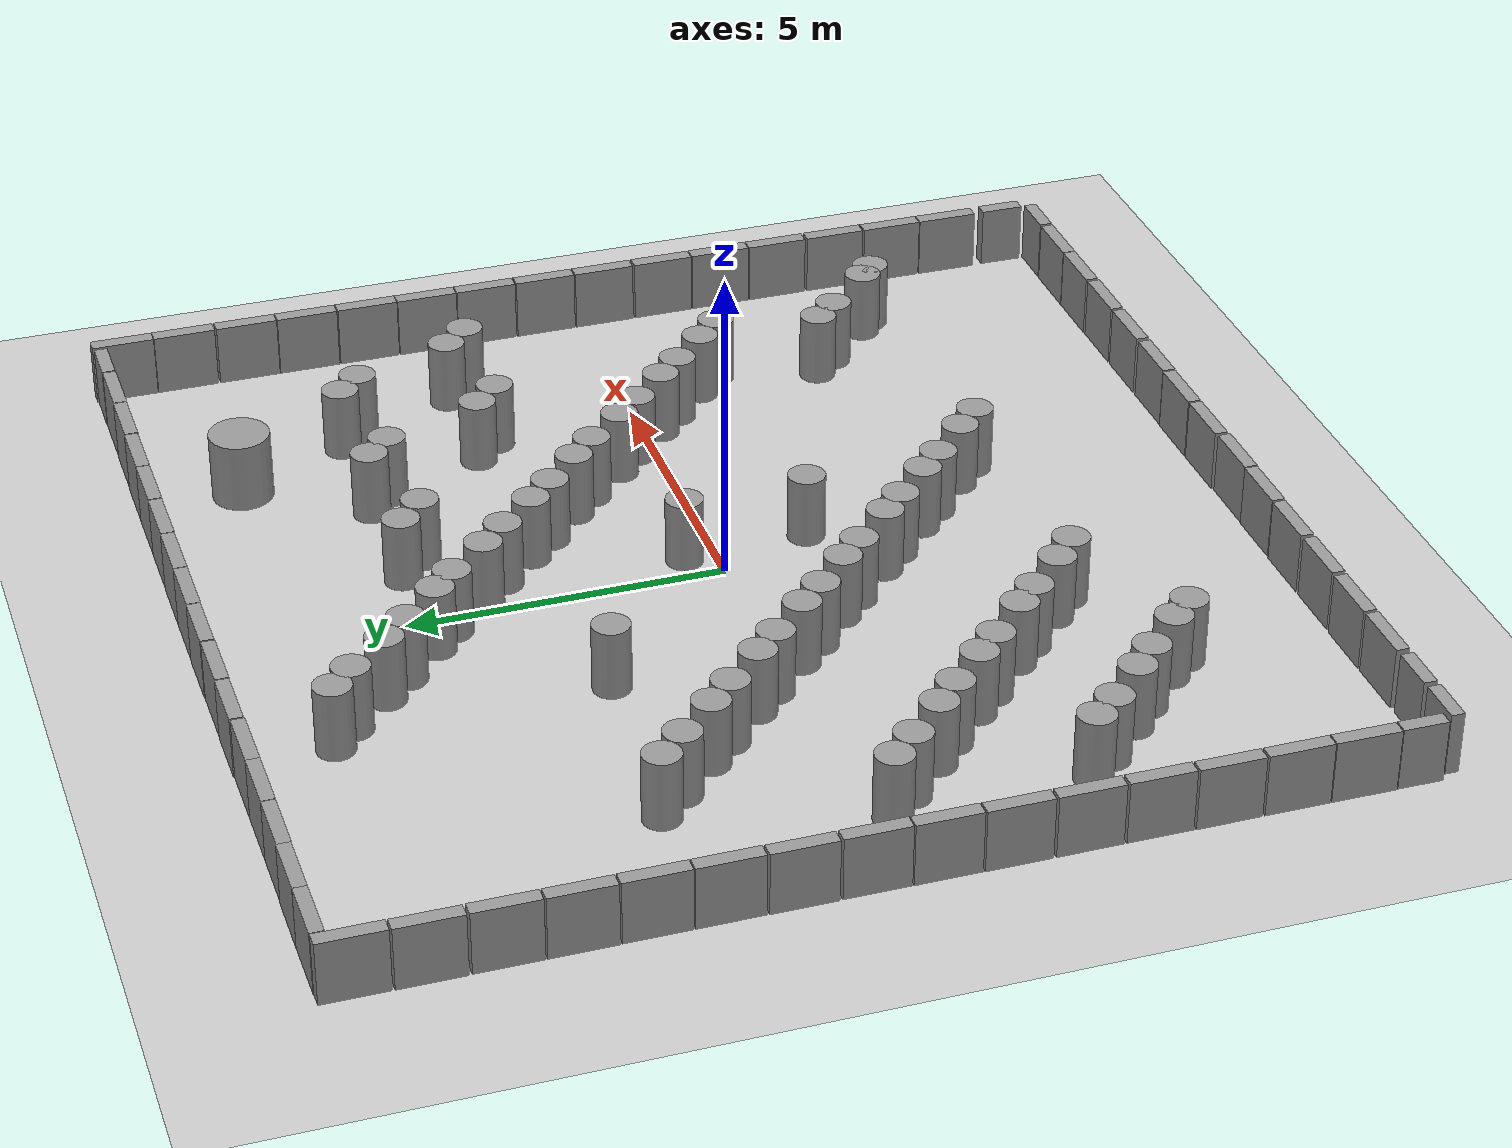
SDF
<sdf version="1.6">
 <world name="default">
  <light name="sun" type="directional">
   <pose>0 0 10 0 -0 0</pose>
   <diffuse>0.8 0.8 0.8 1</diffuse>
   <specular>0.1 0.1 0.1 1</specular>
   <attenuation>
    <range>1000</range>
    <constant>0.9</constant>
    <linear>0.01</linear>
    <quadratic>0.001</quadratic>
   </attenuation>
   <direction>-0.5 0.5 -1</direction>
  </light>
  <model name="ground_plane">
   <static>1</static>
   <static>1</static>
   <link name="link">
    <collision name="collision">
     <geometry><plane><normal>0 0 1</normal><size>100 100</size></plane></geometry>
     <surface><friction><ode><mu>100</mu><mu2>50</mu2></ode></friction></surface>
    </collision>
    <visual name="visual">
     <cast_shadows>0</cast_shadows>
     <geometry><plane><normal>0 0 1</normal><size>100 100</size></plane></geometry>
     <material>
      <script><uri>file://media/materials/scripts/gazebo.material</uri><name>Gazebo/Grey</name></script>
     </material>
    </visual>
   </link>
  </model>
  <gravity>0 0 -9.8</gravity>
  <magnetic_field>6e-06 2.3e-05 -4.2e-05</magnetic_field>
  <atmosphere type="adiabatic"/>
  <physics name="default_physics" default="0" type="ode">
   <max_step_size>0.001</max_step_size>
   <real_time_factor>1</real_time_factor>
   <real_time_update_rate>1000</real_time_update_rate>
  </physics>
  <scene><ambient>0.4 0.4 0.4 1</ambient><background>0.7 0.7 0.7 1</background><shadows>1</shadows></scene>
  <spherical_coordinates>
   <surface_model>EARTH_WGS84</surface_model>
   <latitude_deg>0</latitude_deg>
   <longitude_deg>0</longitude_deg>
   <elevation>0</elevation>
   <heading_deg>0</heading_deg>
  </spherical_coordinates>
  <audio><device>default</device></audio>
  <model name="unit_box_clone">
   <pose>-7.49845 8.12002 0.499999 -1e-06 2e-06 0.00043</pose>
   <link name="link">
    <inertial>
     <mass>1</mass>
     <inertia>
      <ixx>0.166667</ixx>
      <ixy>0</ixy>
      <ixz>0</ixz>
      <iyy>0.166667</iyy>
      <iyz>0</iyz>
      <izz>0.166667</izz>
     </inertia>
    </inertial>
    <collision name="collision"><geometry><box><size>1 0.210541 1</size></box></geometry></collision>
    <visual name="visual">
     <geometry><box><size>1 0.210541 1</size></box></geometry>
     <material>
      <script><name>Gazebo/Grey</name><uri>file://media/materials/scripts/gazebo.material</uri></script>
     </material>
    </visual>
   </link>
  </model>
  <model name="unit_box_clone_0">
   <pose>-6.49724 8.11954 0.499999 1e-06 -2e-06 -0.002361</pose>
   <link name="link">
    <inertial>
     <mass>1</mass>
     <inertia>
      <ixx>0.166667</ixx>
      <ixy>0</ixy>
      <ixz>0</ixz>
      <iyy>0.166667</iyy>
      <iyz>0</iyz>
      <izz>0.166667</izz>
     </inertia>
    </inertial>
    <collision name="collision"><geometry><box><size>1 0.210541 1</size></box></geometry></collision>
    <visual name="visual">
     <geometry><box><size>1 0.210541 1</size></box></geometry>
     <material>
      <script><name>Gazebo/Grey</name><uri>file://media/materials/scripts/gazebo.material</uri></script>
     </material>
    </visual>
   </link>
  </model>
  <model name="unit_box_clone_1">
   <pose>-5.49722 8.10835 0.499999 1e-06 2e-06 -0.002535</pose>
   <link name="link">
    <inertial>
     <mass>1</mass>
     <inertia>
      <ixx>0.166667</ixx>
      <ixy>0</ixy>
      <ixz>0</ixz>
      <iyy>0.166667</iyy>
      <iyz>0</iyz>
      <izz>0.166667</izz>
     </inertia>
    </inertial>
    <collision name="collision"><geometry><box><size>1 0.210541 1</size></box></geometry></collision>
    <visual name="visual">
     <geometry><box><size>1 0.210541 1</size></box></geometry>
     <material>
      <script><name>Gazebo/Grey</name><uri>file://media/materials/scripts/gazebo.material</uri></script>
     </material>
    </visual>
   </link>
  </model>
  <model name="unit_box_clone_4">
   <pose>-2.46316 8.11871 0.499999 -1e-06 2e-06 0.00043</pose>
   <link name="link">
    <inertial>
     <mass>1</mass>
     <inertia>
      <ixx>0.166667</ixx>
      <ixy>0</ixy>
      <ixz>0</ixz>
      <iyy>0.166667</iyy>
      <iyz>0</iyz>
      <izz>0.166667</izz>
     </inertia>
    </inertial>
    <collision name="collision"><geometry><box><size>1 0.210541 1</size></box></geometry></collision>
    <visual name="visual">
     <geometry><box><size>1 0.210541 1</size></box></geometry>
     <material>
      <script><name>Gazebo/Grey</name><uri>file://media/materials/scripts/gazebo.material</uri></script>
     </material>
    </visual>
   </link>
  </model>
  <model name="unit_box_clone_5">
   <pose>-1.44425 8.11205 0.499999 -1e-06 2e-06 0.00043</pose>
   <link name="link">
    <inertial>
     <mass>1</mass>
     <inertia>
      <ixx>0.166667</ixx>
      <ixy>0</ixy>
      <ixz>0</ixz>
      <iyy>0.166667</iyy>
      <iyz>0</iyz>
      <izz>0.166667</izz>
     </inertia>
    </inertial>
    <collision name="collision"><geometry><box><size>1 0.210541 1</size></box></geometry></collision>
    <visual name="visual">
     <geometry><box><size>1 0.210541 1</size></box></geometry>
     <material>
      <script><name>Gazebo/Grey</name><uri>file://media/materials/scripts/gazebo.material</uri></script>
     </material>
    </visual>
   </link>
  </model>
  <model name="unit_box_clone_6">
   <pose>-0.418677 8.1187 0.499999 -1e-06 2e-06 0.00043</pose>
   <link name="link">
    <inertial>
     <mass>1</mass>
     <inertia>
      <ixx>0.166667</ixx>
      <ixy>0</ixy>
      <ixz>0</ixz>
      <iyy>0.166667</iyy>
      <iyz>0</iyz>
      <izz>0.166667</izz>
     </inertia>
    </inertial>
    <collision name="collision"><geometry><box><size>1 0.210541 1</size></box></geometry></collision>
    <visual name="visual">
     <geometry><box><size>1 0.210541 1</size></box></geometry>
     <material>
      <script><name>Gazebo/Grey</name><uri>file://media/materials/scripts/gazebo.material</uri></script>
     </material>
    </visual>
   </link>
  </model>
  <model name="unit_box_clone_7">
   <pose>0.592842 8.11157 0.499999 -1e-06 2e-06 0.00043</pose>
   <link name="link">
    <inertial>
     <mass>1</mass>
     <inertia>
      <ixx>0.166667</ixx>
      <ixy>0</ixy>
      <ixz>0</ixz>
      <iyy>0.166667</iyy>
      <iyz>0</iyz>
      <izz>0.166667</izz>
     </inertia>
    </inertial>
    <collision name="collision"><geometry><box><size>1 0.210541 1</size></box></geometry></collision>
    <visual name="visual">
     <geometry><box><size>1 0.210541 1</size></box></geometry>
     <material>
      <script><name>Gazebo/Grey</name><uri>file://media/materials/scripts/gazebo.material</uri></script>
     </material>
    </visual>
   </link>
  </model>
  <model name="unit_box_clone_8">
   <pose>1.60043 8.11008 0.499999 -1e-06 2e-06 0.00043</pose>
   <link name="link">
    <inertial>
     <mass>1</mass>
     <inertia>
      <ixx>0.166667</ixx>
      <ixy>0</ixy>
      <ixz>0</ixz>
      <iyy>0.166667</iyy>
      <iyz>0</iyz>
      <izz>0.166667</izz>
     </inertia>
    </inertial>
    <collision name="collision"><geometry><box><size>1 0.210541 1</size></box></geometry></collision>
    <visual name="visual">
     <geometry><box><size>1 0.210541 1</size></box></geometry>
     <material>
      <script><name>Gazebo/Grey</name><uri>file://media/materials/scripts/gazebo.material</uri></script>
     </material>
    </visual>
   </link>
  </model>
  <model name="unit_box_clone_9">
   <pose>2.60987 8.10289 0.499999 -1e-06 2e-06 0.00043</pose>
   <link name="link">
    <inertial>
     <mass>1</mass>
     <inertia>
      <ixx>0.166667</ixx>
      <ixy>0</ixy>
      <ixz>0</ixz>
      <iyy>0.166667</iyy>
      <iyz>0</iyz>
      <izz>0.166667</izz>
     </inertia>
    </inertial>
    <collision name="collision"><geometry><box><size>1 0.210541 1</size></box></geometry></collision>
    <visual name="visual">
     <geometry><box><size>1 0.210541 1</size></box></geometry>
     <material>
      <script><name>Gazebo/Grey</name><uri>file://media/materials/scripts/gazebo.material</uri></script>
     </material>
    </visual>
   </link>
  </model>
  <model name="unit_box_clone_10">
   <pose>3.62649 8.09929 0.499999 -1e-06 2e-06 0.00043</pose>
   <link name="link">
    <inertial>
     <mass>1</mass>
     <inertia>
      <ixx>0.166667</ixx>
      <ixy>0</ixy>
      <ixz>0</ixz>
      <iyy>0.166667</iyy>
      <iyz>0</iyz>
      <izz>0.166667</izz>
     </inertia>
    </inertial>
    <collision name="collision"><geometry><box><size>1 0.210541 1</size></box></geometry></collision>
    <visual name="visual">
     <geometry><box><size>1 0.210541 1</size></box></geometry>
     <material>
      <script><name>Gazebo/Grey</name><uri>file://media/materials/scripts/gazebo.material</uri></script>
     </material>
    </visual>
   </link>
  </model>
  <model name="unit_box_clone_11">
   <pose>4.63312 8.09533 0.499999 1e-06 2e-06 -0.003028</pose>
   <link name="link">
    <inertial>
     <mass>1</mass>
     <inertia>
      <ixx>0.166667</ixx>
      <ixy>0</ixy>
      <ixz>0</ixz>
      <iyy>0.166667</iyy>
      <iyz>0</iyz>
      <izz>0.166667</izz>
     </inertia>
    </inertial>
    <collision name="collision"><geometry><box><size>1 0.210541 1</size></box></geometry></collision>
    <visual name="visual">
     <geometry><box><size>1 0.210541 1</size></box></geometry>
     <material>
      <script><name>Gazebo/Grey</name><uri>file://media/materials/scripts/gazebo.material</uri></script>
     </material>
    </visual>
   </link>
  </model>
  <model name="unit_box_0_clone_0">
   <pose>8.11522 6.68459 0.5 1e-06 -1e-06 -0.000246</pose>
   <link name="link">
    <inertial>
     <mass>1</mass>
     <inertia>
      <ixx>0.166667</ixx>
      <ixy>0</ixy>
      <ixz>0</ixz>
      <iyy>0.166667</iyy>
      <iyz>0</iyz>
      <izz>0.166667</izz>
     </inertia>
    </inertial>
    <collision name="collision"><geometry><box><size>0.230819 1 1</size></box></geometry></collision>
    <visual name="visual">
     <geometry><box><size>0.230819 1 1</size></box></geometry>
     <material>
      <script><name>Gazebo/Grey</name><uri>file://media/materials/scripts/gazebo.material</uri></script>
     </material>
    </visual>
   </link>
  </model>
  <model name="unit_box_0_clone_1">
   <pose>8.11915 5.6517 0.5 -1e-06 -1e-06 0.000125</pose>
   <link name="link">
    <inertial>
     <mass>1</mass>
     <inertia>
      <ixx>0.166667</ixx>
      <ixy>0</ixy>
      <ixz>0</ixz>
      <iyy>0.166667</iyy>
      <iyz>0</iyz>
      <izz>0.166667</izz>
     </inertia>
    </inertial>
    <collision name="collision"><geometry><box><size>0.230819 1 1</size></box></geometry></collision>
    <visual name="visual">
     <geometry><box><size>0.230819 1 1</size></box></geometry>
     <material>
      <script><name>Gazebo/Grey</name><uri>file://media/materials/scripts/gazebo.material</uri></script>
     </material>
    </visual>
   </link>
  </model>
  <model name="unit_box_0_clone_2">
   <pose>8.11914 4.64016 0.5 1e-06 1e-06 0.00014</pose>
   <link name="link">
    <inertial>
     <mass>1</mass>
     <inertia>
      <ixx>0.166667</ixx>
      <ixy>0</ixy>
      <ixz>0</ixz>
      <iyy>0.166667</iyy>
      <iyz>0</iyz>
      <izz>0.166667</izz>
     </inertia>
    </inertial>
    <collision name="collision"><geometry><box><size>0.230819 1 1</size></box></geometry></collision>
    <visual name="visual">
     <geometry><box><size>0.230819 1 1</size></box></geometry>
     <material>
      <script><name>Gazebo/Grey</name><uri>file://media/materials/scripts/gazebo.material</uri></script>
     </material>
    </visual>
   </link>
  </model>
  <model name="unit_box_0_clone_3">
   <pose>8.11914 3.62226 0.5 1e-06 1e-06 0.000121</pose>
   <link name="link">
    <inertial>
     <mass>1</mass>
     <inertia>
      <ixx>0.166667</ixx>
      <ixy>0</ixy>
      <ixz>0</ixz>
      <iyy>0.166667</iyy>
      <iyz>0</iyz>
      <izz>0.166667</izz>
     </inertia>
    </inertial>
    <collision name="collision"><geometry><box><size>0.230819 1 1</size></box></geometry></collision>
    <visual name="visual">
     <geometry><box><size>0.230819 1 1</size></box></geometry>
     <material>
      <script><name>Gazebo/Grey</name><uri>file://media/materials/scripts/gazebo.material</uri></script>
     </material>
    </visual>
   </link>
  </model>
  <model name="unit_box_0_clone_4">
   <pose>8.11332 2.61062 0.5 -1e-06 1e-06 -0.001217</pose>
   <link name="link">
    <inertial>
     <mass>1</mass>
     <inertia>
      <ixx>0.166667</ixx>
      <ixy>0</ixy>
      <ixz>0</ixz>
      <iyy>0.166667</iyy>
      <iyz>0</iyz>
      <izz>0.166667</izz>
     </inertia>
    </inertial>
    <collision name="collision"><geometry><box><size>0.230819 1 1</size></box></geometry></collision>
    <visual name="visual">
     <geometry><box><size>0.230819 1 1</size></box></geometry>
     <material>
      <script><name>Gazebo/Grey</name><uri>file://media/materials/scripts/gazebo.material</uri></script>
     </material>
    </visual>
   </link>
  </model>
  <model name="unit_box_0_clone_5">
   <pose>8.11277 1.59919 0.5 1e-06 1e-06 0.000121</pose>
   <link name="link">
    <inertial>
     <mass>1</mass>
     <inertia>
      <ixx>0.166667</ixx>
      <ixy>0</ixy>
      <ixz>0</ixz>
      <iyy>0.166667</iyy>
      <iyz>0</iyz>
      <izz>0.166667</izz>
     </inertia>
    </inertial>
    <collision name="collision"><geometry><box><size>0.230819 1 1</size></box></geometry></collision>
    <visual name="visual">
     <geometry><box><size>0.230819 1 1</size></box></geometry>
     <material>
      <script><name>Gazebo/Grey</name><uri>file://media/materials/scripts/gazebo.material</uri></script>
     </material>
    </visual>
   </link>
  </model>
  <model name="unit_box_0_clone_6">
   <pose>8.11277 0.574937 0.5 1e-06 1e-06 0.000121</pose>
   <link name="link">
    <inertial>
     <mass>1</mass>
     <inertia>
      <ixx>0.166667</ixx>
      <ixy>0</ixy>
      <ixz>0</ixz>
      <iyy>0.166667</iyy>
      <iyz>0</iyz>
      <izz>0.166667</izz>
     </inertia>
    </inertial>
    <collision name="collision"><geometry><box><size>0.230819 1 1</size></box></geometry></collision>
    <visual name="visual">
     <geometry><box><size>0.230819 1 1</size></box></geometry>
     <material>
      <script><name>Gazebo/Grey</name><uri>file://media/materials/scripts/gazebo.material</uri></script>
     </material>
    </visual>
   </link>
  </model>
  <model name="unit_box_0_clone_7">
   <pose>8.11276 -0.449321 0.5 1e-06 1e-06 0.000121</pose>
   <link name="link">
    <inertial>
     <mass>1</mass>
     <inertia>
      <ixx>0.166667</ixx>
      <ixy>0</ixy>
      <ixz>0</ixz>
      <iyy>0.166667</iyy>
      <iyz>0</iyz>
      <izz>0.166667</izz>
     </inertia>
    </inertial>
    <collision name="collision"><geometry><box><size>0.230819 1 1</size></box></geometry></collision>
    <visual name="visual">
     <geometry><box><size>0.230819 1 1</size></box></geometry>
     <material>
      <script><name>Gazebo/Grey</name><uri>file://media/materials/scripts/gazebo.material</uri></script>
     </material>
    </visual>
   </link>
  </model>
  <model name="unit_box_0_clone_8">
   <pose>8.11912 -1.48631 0.5 1e-06 1e-06 0.000121</pose>
   <link name="link">
    <inertial>
     <mass>1</mass>
     <inertia>
      <ixx>0.166667</ixx>
      <ixy>0</ixy>
      <ixz>0</ixz>
      <iyy>0.166667</iyy>
      <iyz>0</iyz>
      <izz>0.166667</izz>
     </inertia>
    </inertial>
    <collision name="collision"><geometry><box><size>0.230819 1 1</size></box></geometry></collision>
    <visual name="visual">
     <geometry><box><size>0.230819 1 1</size></box></geometry>
     <material>
      <script><name>Gazebo/Grey</name><uri>file://media/materials/scripts/gazebo.material</uri></script>
     </material>
    </visual>
   </link>
  </model>
  <model name="unit_box_0_clone_9">
   <pose>8.12548 -2.50421 0.5 1e-06 1e-06 0.000121</pose>
   <link name="link">
    <inertial>
     <mass>1</mass>
     <inertia>
      <ixx>0.166667</ixx>
      <ixy>0</ixy>
      <ixz>0</ixz>
      <iyy>0.166667</iyy>
      <iyz>0</iyz>
      <izz>0.166667</izz>
     </inertia>
    </inertial>
    <collision name="collision"><geometry><box><size>0.230819 1 1</size></box></geometry></collision>
    <visual name="visual">
     <geometry><box><size>0.230819 1 1</size></box></geometry>
     <material>
      <script><name>Gazebo/Grey</name><uri>file://media/materials/scripts/gazebo.material</uri></script>
     </material>
    </visual>
   </link>
  </model>
  <model name="unit_box_0_clone_10">
   <pose>8.12331 -3.52223 0.5 1e-06 1e-06 0.000121</pose>
   <link name="link">
    <inertial>
     <mass>1</mass>
     <inertia>
      <ixx>0.166667</ixx>
      <ixy>0</ixy>
      <ixz>0</ixz>
      <iyy>0.166667</iyy>
      <iyz>0</iyz>
      <izz>0.166667</izz>
     </inertia>
    </inertial>
    <collision name="collision"><geometry><box><size>0.230819 1 1</size></box></geometry></collision>
    <visual name="visual">
     <geometry><box><size>0.230819 1 1</size></box></geometry>
     <material>
      <script><name>Gazebo/Grey</name><uri>file://media/materials/scripts/gazebo.material</uri></script>
     </material>
    </visual>
   </link>
  </model>
  <model name="unit_box_0_clone_11">
   <pose>8.1233 -4.56316 0.5 1e-06 1e-06 0.000121</pose>
   <link name="link">
    <inertial>
     <mass>1</mass>
     <inertia>
      <ixx>0.166667</ixx>
      <ixy>0</ixy>
      <ixz>0</ixz>
      <iyy>0.166667</iyy>
      <iyz>0</iyz>
      <izz>0.166667</izz>
     </inertia>
    </inertial>
    <collision name="collision"><geometry><box><size>0.230819 1 1</size></box></geometry></collision>
    <visual name="visual">
     <geometry><box><size>0.230819 1 1</size></box></geometry>
     <material>
      <script><name>Gazebo/Grey</name><uri>file://media/materials/scripts/gazebo.material</uri></script>
     </material>
    </visual>
   </link>
  </model>
  <model name="unit_box_0_clone_12">
   <pose>8.11815 -5.59378 0.5 1e-06 1e-06 0.000121</pose>
   <link name="link">
    <inertial>
     <mass>1</mass>
     <inertia>
      <ixx>0.166667</ixx>
      <ixy>0</ixy>
      <ixz>0</ixz>
      <iyy>0.166667</iyy>
      <iyz>0</iyz>
      <izz>0.166667</izz>
     </inertia>
    </inertial>
    <collision name="collision"><geometry><box><size>0.230819 1 1</size></box></geometry></collision>
    <visual name="visual">
     <geometry><box><size>0.230819 1 1</size></box></geometry>
     <material>
      <script><name>Gazebo/Grey</name><uri>file://media/materials/scripts/gazebo.material</uri></script>
     </material>
    </visual>
   </link>
  </model>
  <model name="unit_box_0_clone_13">
   <pose>8.11333 -6.60776 0.5 -1e-06 1e-06 -0.005393</pose>
   <link name="link">
    <inertial>
     <mass>1</mass>
     <inertia>
      <ixx>0.166667</ixx>
      <ixy>0</ixy>
      <ixz>0</ixz>
      <iyy>0.166667</iyy>
      <iyz>0</iyz>
      <izz>0.166667</izz>
     </inertia>
    </inertial>
    <collision name="collision"><geometry><box><size>0.230819 1 1</size></box></geometry></collision>
    <visual name="visual">
     <geometry><box><size>0.230819 1 1</size></box></geometry>
     <material>
      <script><name>Gazebo/Grey</name><uri>file://media/materials/scripts/gazebo.material</uri></script>
     </material>
    </visual>
   </link>
  </model>
  <model name="unit_box_clone_15_clone_0">
   <pose>6.71207 -8.13102 0.499999 -1e-06 2e-06 0.00043</pose>
   <link name="link">
    <inertial>
     <mass>1</mass>
     <inertia>
      <ixx>0.166667</ixx>
      <ixy>0</ixy>
      <ixz>0</ixz>
      <iyy>0.166667</iyy>
      <iyz>0</iyz>
      <izz>0.166667</izz>
     </inertia>
    </inertial>
    <collision name="collision"><geometry><box><size>1 0.210541 1</size></box></geometry></collision>
    <visual name="visual">
     <geometry><box><size>1 0.210541 1</size></box></geometry>
     <material>
      <script><name>Gazebo/Grey</name><uri>file://media/materials/scripts/gazebo.material</uri></script>
     </material>
    </visual>
   </link>
  </model>
  <model name="unit_box_clone_15_clone_1">
   <pose>5.69715 -8.13101 0.499999 -1e-06 2e-06 0.00043</pose>
   <link name="link">
    <inertial>
     <mass>1</mass>
     <inertia>
      <ixx>0.166667</ixx>
      <ixy>0</ixy>
      <ixz>0</ixz>
      <iyy>0.166667</iyy>
      <iyz>0</iyz>
      <izz>0.166667</izz>
     </inertia>
    </inertial>
    <collision name="collision"><geometry><box><size>1 0.210541 1</size></box></geometry></collision>
    <visual name="visual">
     <geometry><box><size>1 0.210541 1</size></box></geometry>
     <material>
      <script><name>Gazebo/Grey</name><uri>file://media/materials/scripts/gazebo.material</uri></script>
     </material>
    </visual>
   </link>
  </model>
  <model name="unit_box_clone_15_clone_2">
   <pose>4.63881 -8.1372 0.499999 -1e-06 2e-06 0.00043</pose>
   <link name="link">
    <inertial>
     <mass>1</mass>
     <inertia>
      <ixx>0.166667</ixx>
      <ixy>0</ixy>
      <ixz>0</ixz>
      <iyy>0.166667</iyy>
      <iyz>0</iyz>
      <izz>0.166667</izz>
     </inertia>
    </inertial>
    <collision name="collision"><geometry><box><size>1 0.210541 1</size></box></geometry></collision>
    <visual name="visual">
     <geometry><box><size>1 0.210541 1</size></box></geometry>
     <material>
      <script><name>Gazebo/Grey</name><uri>file://media/materials/scripts/gazebo.material</uri></script>
     </material>
    </visual>
   </link>
  </model>
  <model name="unit_box_clone_15_clone_3">
   <pose>3.57975 -8.1372 0.499999 -1e-06 2e-06 0.00043</pose>
   <link name="link">
    <inertial>
     <mass>1</mass>
     <inertia>
      <ixx>0.166667</ixx>
      <ixy>0</ixy>
      <ixz>0</ixz>
      <iyy>0.166667</iyy>
      <iyz>0</iyz>
      <izz>0.166667</izz>
     </inertia>
    </inertial>
    <collision name="collision"><geometry><box><size>1 0.210541 1</size></box></geometry></collision>
    <visual name="visual">
     <geometry><box><size>1 0.210541 1</size></box></geometry>
     <material>
      <script><name>Gazebo/Grey</name><uri>file://media/materials/scripts/gazebo.material</uri></script>
     </material>
    </visual>
   </link>
  </model>
  <model name="unit_box_clone_15_clone_4">
   <pose>2.49815 -8.13719 0.499999 -1e-06 2e-06 0.00043</pose>
   <link name="link">
    <inertial>
     <mass>1</mass>
     <inertia>
      <ixx>0.166667</ixx>
      <ixy>0</ixy>
      <ixz>0</ixz>
      <iyy>0.166667</iyy>
      <iyz>0</iyz>
      <izz>0.166667</izz>
     </inertia>
    </inertial>
    <collision name="collision"><geometry><box><size>1 0.210541 1</size></box></geometry></collision>
    <visual name="visual">
     <geometry><box><size>1 0.210541 1</size></box></geometry>
     <material>
      <script><name>Gazebo/Grey</name><uri>file://media/materials/scripts/gazebo.material</uri></script>
     </material>
    </visual>
   </link>
  </model>
  <model name="unit_box_clone_15_clone_5">
   <pose>1.46162 -8.12592 0.499999 -1e-06 2e-06 0.00043</pose>
   <link name="link">
    <inertial>
     <mass>1</mass>
     <inertia>
      <ixx>0.166667</ixx>
      <ixy>0</ixy>
      <ixz>0</ixz>
      <iyy>0.166667</iyy>
      <iyz>0</iyz>
      <izz>0.166667</izz>
     </inertia>
    </inertial>
    <collision name="collision"><geometry><box><size>1 0.210541 1</size></box></geometry></collision>
    <visual name="visual">
     <geometry><box><size>1 0.210541 1</size></box></geometry>
     <material>
      <script><name>Gazebo/Grey</name><uri>file://media/materials/scripts/gazebo.material</uri></script>
     </material>
    </visual>
   </link>
  </model>
  <model name="unit_box_clone_15_clone_6">
   <pose>0.425095 -8.1259 0.499999 -1e-06 2e-06 0.00043</pose>
   <link name="link">
    <inertial>
     <mass>1</mass>
     <inertia>
      <ixx>0.166667</ixx>
      <ixy>0</ixy>
      <ixz>0</ixz>
      <iyy>0.166667</iyy>
      <iyz>0</iyz>
      <izz>0.166667</izz>
     </inertia>
    </inertial>
    <collision name="collision"><geometry><box><size>1 0.210541 1</size></box></geometry></collision>
    <visual name="visual">
     <geometry><box><size>1 0.210541 1</size></box></geometry>
     <material>
      <script><name>Gazebo/Grey</name><uri>file://media/materials/scripts/gazebo.material</uri></script>
     </material>
    </visual>
   </link>
  </model>
  <model name="unit_box_clone_15_clone_7">
   <pose>-0.633967 -8.14846 0.499999 -1e-06 2e-06 0.00043</pose>
   <link name="link">
    <inertial>
     <mass>1</mass>
     <inertia>
      <ixx>0.166667</ixx>
      <ixy>0</ixy>
      <ixz>0</ixz>
      <iyy>0.166667</iyy>
      <iyz>0</iyz>
      <izz>0.166667</izz>
     </inertia>
    </inertial>
    <collision name="collision"><geometry><box><size>1 0.210541 1</size></box></geometry></collision>
    <visual name="visual">
     <geometry><box><size>1 0.210541 1</size></box></geometry>
     <material>
      <script><name>Gazebo/Grey</name><uri>file://media/materials/scripts/gazebo.material</uri></script>
     </material>
    </visual>
   </link>
  </model>
  <model name="unit_box_clone_15_clone_8">
   <pose>-1.65923 -8.13717 0.499999 -1e-06 2e-06 0.00043</pose>
   <link name="link">
    <inertial>
     <mass>1</mass>
     <inertia>
      <ixx>0.166667</ixx>
      <ixy>0</ixy>
      <ixz>0</ixz>
      <iyy>0.166667</iyy>
      <iyz>0</iyz>
      <izz>0.166667</izz>
     </inertia>
    </inertial>
    <collision name="collision"><geometry><box><size>1 0.210541 1</size></box></geometry></collision>
    <visual name="visual">
     <geometry><box><size>1 0.210541 1</size></box></geometry>
     <material>
      <script><name>Gazebo/Grey</name><uri>file://media/materials/scripts/gazebo.material</uri></script>
     </material>
    </visual>
   </link>
  </model>
  <model name="unit_box_clone_15_clone_9">
   <pose>-2.70703 -8.12593 0.499999 -1e-06 2e-06 0.00043</pose>
   <link name="link">
    <inertial>
     <mass>1</mass>
     <inertia>
      <ixx>0.166667</ixx>
      <ixy>0</ixy>
      <ixz>0</ixz>
      <iyy>0.166667</iyy>
      <iyz>0</iyz>
      <izz>0.166667</izz>
     </inertia>
    </inertial>
    <collision name="collision"><geometry><box><size>1 0.210541 1</size></box></geometry></collision>
    <visual name="visual">
     <geometry><box><size>1 0.210541 1</size></box></geometry>
     <material>
      <script><name>Gazebo/Grey</name><uri>file://media/materials/scripts/gazebo.material</uri></script>
     </material>
    </visual>
   </link>
  </model>
  <model name="unit_box_clone_15_clone_10">
   <pose>-3.77736 -8.12592 0.499999 -1e-06 2e-06 0.00043</pose>
   <link name="link">
    <inertial>
     <mass>1</mass>
     <inertia>
      <ixx>0.166667</ixx>
      <ixy>0</ixy>
      <ixz>0</ixz>
      <iyy>0.166667</iyy>
      <iyz>0</iyz>
      <izz>0.166667</izz>
     </inertia>
    </inertial>
    <collision name="collision"><geometry><box><size>1 0.210541 1</size></box></geometry></collision>
    <visual name="visual">
     <geometry><box><size>1 0.210541 1</size></box></geometry>
     <material>
      <script><name>Gazebo/Grey</name><uri>file://media/materials/scripts/gazebo.material</uri></script>
     </material>
    </visual>
   </link>
  </model>
  <model name="unit_box_clone_15_clone_11">
   <pose>-4.85896 -8.11466 0.499999 -1e-06 2e-06 0.00043</pose>
   <link name="link">
    <inertial>
     <mass>1</mass>
     <inertia>
      <ixx>0.166667</ixx>
      <ixy>0</ixy>
      <ixz>0</ixz>
      <iyy>0.166667</iyy>
      <iyz>0</iyz>
      <izz>0.166667</izz>
     </inertia>
    </inertial>
    <collision name="collision"><geometry><box><size>1 0.210541 1</size></box></geometry></collision>
    <visual name="visual">
     <geometry><box><size>1 0.210541 1</size></box></geometry>
     <material>
      <script><name>Gazebo/Grey</name><uri>file://media/materials/scripts/gazebo.material</uri></script>
     </material>
    </visual>
   </link>
  </model>
  <model name="unit_box_clone_15_clone_12">
   <pose>-5.91802 -8.11464 0.499999 -1e-06 2e-06 0.00043</pose>
   <link name="link">
    <inertial>
     <mass>1</mass>
     <inertia>
      <ixx>0.166667</ixx>
      <ixy>0</ixy>
      <ixz>0</ixz>
      <iyy>0.166667</iyy>
      <iyz>0</iyz>
      <izz>0.166667</izz>
     </inertia>
    </inertial>
    <collision name="collision"><geometry><box><size>1 0.210541 1</size></box></geometry></collision>
    <visual name="visual">
     <geometry><box><size>1 0.210541 1</size></box></geometry>
     <material>
      <script><name>Gazebo/Grey</name><uri>file://media/materials/scripts/gazebo.material</uri></script>
     </material>
    </visual>
   </link>
  </model>
  <model name="unit_box_0_clone_4_clone">
   <pose>-8.12647 7.71768 0.5 1e-06 1e-06 0.000121</pose>
   <link name="link">
    <inertial>
     <mass>1</mass>
     <inertia>
      <ixx>0.166667</ixx>
      <ixy>0</ixy>
      <ixz>0</ixz>
      <iyy>0.166667</iyy>
      <iyz>0</iyz>
      <izz>0.166667</izz>
     </inertia>
    </inertial>
    <collision name="collision"><geometry><box><size>0.230819 1 1</size></box></geometry></collision>
    <visual name="visual">
     <geometry><box><size>0.230819 1 1</size></box></geometry>
     <material>
      <script><name>Gazebo/Grey</name><uri>file://media/materials/scripts/gazebo.material</uri></script>
     </material>
    </visual>
   </link>
  </model>
  <model name="unit_box_0_clone_4_clone_0">
   <pose>-8.13281 6.68714 0.5 1e-06 1e-06 0.000121</pose>
   <link name="link">
    <inertial>
     <mass>1</mass>
     <inertia>
      <ixx>0.166667</ixx>
      <ixy>0</ixy>
      <ixz>0</ixz>
      <iyy>0.166667</iyy>
      <iyz>0</iyz>
      <izz>0.166667</izz>
     </inertia>
    </inertial>
    <collision name="collision"><geometry><box><size>0.230819 1 1</size></box></geometry></collision>
    <visual name="visual">
     <geometry><box><size>0.230819 1 1</size></box></geometry>
     <material>
      <script><name>Gazebo/Grey</name><uri>file://media/materials/scripts/gazebo.material</uri></script>
     </material>
    </visual>
   </link>
  </model>
  <model name="unit_box_0_clone_4_clone_1">
   <pose>-8.12606 5.64722 0.5 1e-06 1e-06 0.000121</pose>
   <link name="link">
    <inertial>
     <mass>1</mass>
     <inertia>
      <ixx>0.166667</ixx>
      <ixy>0</ixy>
      <ixz>0</ixz>
      <iyy>0.166667</iyy>
      <iyz>0</iyz>
      <izz>0.166667</izz>
     </inertia>
    </inertial>
    <collision name="collision"><geometry><box><size>0.230819 1 1</size></box></geometry></collision>
    <visual name="visual">
     <geometry><box><size>0.230819 1 1</size></box></geometry>
     <material>
      <script><name>Gazebo/Grey</name><uri>file://media/materials/scripts/gazebo.material</uri></script>
     </material>
    </visual>
   </link>
  </model>
  <model name="unit_box_0_clone_4_clone_2">
   <pose>-8.12607 4.6208 0.5 1e-06 1e-06 0.000121</pose>
   <link name="link">
    <inertial>
     <mass>1</mass>
     <inertia>
      <ixx>0.166667</ixx>
      <ixy>0</ixy>
      <ixz>0</ixz>
      <iyy>0.166667</iyy>
      <iyz>0</iyz>
      <izz>0.166667</izz>
     </inertia>
    </inertial>
    <collision name="collision"><geometry><box><size>0.230819 1 1</size></box></geometry></collision>
    <visual name="visual">
     <geometry><box><size>0.230819 1 1</size></box></geometry>
     <material>
      <script><name>Gazebo/Grey</name><uri>file://media/materials/scripts/gazebo.material</uri></script>
     </material>
    </visual>
   </link>
  </model>
  <model name="unit_box_0_clone_4_clone_3">
   <pose>-8.11932 3.59438 0.5 1e-06 1e-06 0.000121</pose>
   <link name="link">
    <inertial>
     <mass>1</mass>
     <inertia>
      <ixx>0.166667</ixx>
      <ixy>0</ixy>
      <ixz>0</ixz>
      <iyy>0.166667</iyy>
      <iyz>0</iyz>
      <izz>0.166667</izz>
     </inertia>
    </inertial>
    <collision name="collision"><geometry><box><size>0.230819 1 1</size></box></geometry></collision>
    <visual name="visual">
     <geometry><box><size>0.230819 1 1</size></box></geometry>
     <material>
      <script><name>Gazebo/Grey</name><uri>file://media/materials/scripts/gazebo.material</uri></script>
     </material>
    </visual>
   </link>
  </model>
  <model name="unit_box_0_clone_4_clone_4">
   <pose>-8.11932 2.57472 0.5 1e-06 1e-06 0.000121</pose>
   <link name="link">
    <inertial>
     <mass>1</mass>
     <inertia>
      <ixx>0.166667</ixx>
      <ixy>0</ixy>
      <ixz>0</ixz>
      <iyy>0.166667</iyy>
      <iyz>0</iyz>
      <izz>0.166667</izz>
     </inertia>
    </inertial>
    <collision name="collision"><geometry><box><size>0.230819 1 1</size></box></geometry></collision>
    <visual name="visual">
     <geometry><box><size>0.230819 1 1</size></box></geometry>
     <material>
      <script><name>Gazebo/Grey</name><uri>file://media/materials/scripts/gazebo.material</uri></script>
     </material>
    </visual>
   </link>
  </model>
  <model name="unit_box_0_clone_4_clone_5">
   <pose>-8.12608 1.54155 0.5 1e-06 1e-06 0.000121</pose>
   <link name="link">
    <inertial>
     <mass>1</mass>
     <inertia>
      <ixx>0.166667</ixx>
      <ixy>0</ixy>
      <ixz>0</ixz>
      <iyy>0.166667</iyy>
      <iyz>0</iyz>
      <izz>0.166667</izz>
     </inertia>
    </inertial>
    <collision name="collision"><geometry><box><size>0.230819 1 1</size></box></geometry></collision>
    <visual name="visual">
     <geometry><box><size>0.230819 1 1</size></box></geometry>
     <material>
      <script><name>Gazebo/Grey</name><uri>file://media/materials/scripts/gazebo.material</uri></script>
     </material>
    </visual>
   </link>
  </model>
  <model name="unit_box_0_clone_4_clone_6">
   <pose>-8.11933 0.501629 0.5 1e-06 1e-06 0.000121</pose>
   <link name="link">
    <inertial>
     <mass>1</mass>
     <inertia>
      <ixx>0.166667</ixx>
      <ixy>0</ixy>
      <ixz>0</ixz>
      <iyy>0.166667</iyy>
      <iyz>0</iyz>
      <izz>0.166667</izz>
     </inertia>
    </inertial>
    <collision name="collision"><geometry><box><size>0.230819 1 1</size></box></geometry></collision>
    <visual name="visual">
     <geometry><box><size>0.230819 1 1</size></box></geometry>
     <material>
      <script><name>Gazebo/Grey</name><uri>file://media/materials/scripts/gazebo.material</uri></script>
     </material>
    </visual>
   </link>
  </model>
  <model name="unit_box_0_clone_4_clone_7">
   <pose>-8.12609 -0.518035 0.5 1e-06 1e-06 0.000121</pose>
   <link name="link">
    <inertial>
     <mass>1</mass>
     <inertia>
      <ixx>0.166667</ixx>
      <ixy>0</ixy>
      <ixz>0</ixz>
      <iyy>0.166667</iyy>
      <iyz>0</iyz>
      <izz>0.166667</izz>
     </inertia>
    </inertial>
    <collision name="collision"><geometry><box><size>0.230819 1 1</size></box></geometry></collision>
    <visual name="visual">
     <geometry><box><size>0.230819 1 1</size></box></geometry>
     <material>
      <script><name>Gazebo/Grey</name><uri>file://media/materials/scripts/gazebo.material</uri></script>
     </material>
    </visual>
   </link>
  </model>
  <model name="unit_box_0_clone_4_clone_8">
   <pose>-8.13284 -1.54446 0.5 1e-06 1e-06 0.000121</pose>
   <link name="link">
    <inertial>
     <mass>1</mass>
     <inertia>
      <ixx>0.166667</ixx>
      <ixy>0</ixy>
      <ixz>0</ixz>
      <iyy>0.166667</iyy>
      <iyz>0</iyz>
      <izz>0.166667</izz>
     </inertia>
    </inertial>
    <collision name="collision"><geometry><box><size>0.230819 1 1</size></box></geometry></collision>
    <visual name="visual">
     <geometry><box><size>0.230819 1 1</size></box></geometry>
     <material>
      <script><name>Gazebo/Grey</name><uri>file://media/materials/scripts/gazebo.material</uri></script>
     </material>
    </visual>
   </link>
  </model>
  <model name="unit_box_0_clone_4_clone_9">
   <pose>-8.13285 -2.58438 0.5 1e-06 1e-06 0.000121</pose>
   <link name="link">
    <inertial>
     <mass>1</mass>
     <inertia>
      <ixx>0.166667</ixx>
      <ixy>0</ixy>
      <ixz>0</ixz>
      <iyy>0.166667</iyy>
      <iyz>0</iyz>
      <izz>0.166667</izz>
     </inertia>
    </inertial>
    <collision name="collision"><geometry><box><size>0.230819 1 1</size></box></geometry></collision>
    <visual name="visual">
     <geometry><box><size>0.230819 1 1</size></box></geometry>
     <material>
      <script><name>Gazebo/Grey</name><uri>file://media/materials/scripts/gazebo.material</uri></script>
     </material>
    </visual>
   </link>
  </model>
  <model name="unit_box_0_clone_4_clone_10">
   <pose>-8.13285 -3.6243 0.5 1e-06 1e-06 0.000121</pose>
   <link name="link">
    <inertial>
     <mass>1</mass>
     <inertia>
      <ixx>0.166667</ixx>
      <ixy>0</ixy>
      <ixz>0</ixz>
      <iyy>0.166667</iyy>
      <iyz>0</iyz>
      <izz>0.166667</izz>
     </inertia>
    </inertial>
    <collision name="collision"><geometry><box><size>0.230819 1 1</size></box></geometry></collision>
    <visual name="visual">
     <geometry><box><size>0.230819 1 1</size></box></geometry>
     <material>
      <script><name>Gazebo/Grey</name><uri>file://media/materials/scripts/gazebo.material</uri></script>
     </material>
    </visual>
   </link>
  </model>
  <model name="unit_box_0_clone_4_clone_11">
   <pose>-8.1396 -4.65747 0.5 1e-06 1e-06 0.000121</pose>
   <link name="link">
    <inertial>
     <mass>1</mass>
     <inertia>
      <ixx>0.166667</ixx>
      <ixy>0</ixy>
      <ixz>0</ixz>
      <iyy>0.166667</iyy>
      <iyz>0</iyz>
      <izz>0.166667</izz>
     </inertia>
    </inertial>
    <collision name="collision"><geometry><box><size>0.230819 1 1</size></box></geometry></collision>
    <visual name="visual">
     <geometry><box><size>0.230819 1 1</size></box></geometry>
     <material>
      <script><name>Gazebo/Grey</name><uri>file://media/materials/scripts/gazebo.material</uri></script>
     </material>
    </visual>
   </link>
  </model>
  <model name="unit_box_0_clone_4_clone_12">
   <pose>-8.1396 -5.69064 0.5 1e-06 1e-06 0.000121</pose>
   <link name="link">
    <inertial>
     <mass>1</mass>
     <inertia>
      <ixx>0.166667</ixx>
      <ixy>0</ixy>
      <ixz>0</ixz>
      <iyy>0.166667</iyy>
      <iyz>0</iyz>
      <izz>0.166667</izz>
     </inertia>
    </inertial>
    <collision name="collision"><geometry><box><size>0.230819 1 1</size></box></geometry></collision>
    <visual name="visual">
     <geometry><box><size>0.230819 1 1</size></box></geometry>
     <material>
      <script><name>Gazebo/Grey</name><uri>file://media/materials/scripts/gazebo.material</uri></script>
     </material>
    </visual>
   </link>
  </model>
  <model name="unit_box_0_clone_4_clone_13">
   <pose>-8.14113 -6.70872 0.5 -1e-06 1e-06 -0.008849</pose>
   <link name="link">
    <inertial>
     <mass>1</mass>
     <inertia>
      <ixx>0.166667</ixx>
      <ixy>0</ixy>
      <ixz>0</ixz>
      <iyy>0.166667</iyy>
      <iyz>0</iyz>
      <izz>0.166667</izz>
     </inertia>
    </inertial>
    <collision name="collision"><geometry><box><size>0.230819 1 1</size></box></geometry></collision>
    <visual name="visual">
     <geometry><box><size>0.230819 1 1</size></box></geometry>
     <material>
      <script><name>Gazebo/Grey</name><uri>file://media/materials/scripts/gazebo.material</uri></script>
     </material>
    </visual>
   </link>
  </model>
  <model name="unit_box_0_clone_0_clone">
   <pose>8.11438 7.69322 0.5 -1e-06 -1e-06 0.000107</pose>
   <link name="link">
    <inertial>
     <mass>1</mass>
     <inertia>
      <ixx>0.166667</ixx>
      <ixy>0</ixy>
      <ixz>0</ixz>
      <iyy>0.166667</iyy>
      <iyz>0</iyz>
      <izz>0.166667</izz>
     </inertia>
    </inertial>
    <collision name="collision"><geometry><box><size>0.230819 1 1</size></box></geometry></collision>
    <visual name="visual">
     <geometry><box><size>0.230819 1 1</size></box></geometry>
     <material>
      <script><name>Gazebo/Grey</name><uri>file://media/materials/scripts/gazebo.material</uri></script>
     </material>
    </visual>
   </link>
  </model>
  <model name="unit_box_clone_11_clone">
   <pose>5.65439 8.08347 0.499999 -1e-06 2e-06 -0.003408</pose>
   <link name="link">
    <inertial>
     <mass>1</mass>
     <inertia>
      <ixx>0.166667</ixx>
      <ixy>0</ixy>
      <ixz>0</ixz>
      <iyy>0.166667</iyy>
      <iyz>0</iyz>
      <izz>0.166667</izz>
     </inertia>
    </inertial>
    <collision name="collision"><geometry><box><size>1 0.210541 1</size></box></geometry></collision>
    <visual name="visual">
     <geometry><box><size>1 0.210541 1</size></box></geometry>
     <material>
      <script><name>Gazebo/Grey</name><uri>file://media/materials/scripts/gazebo.material</uri></script>
     </material>
    </visual>
   </link>
  </model>
  <model name="unit_box_clone_11_clone_0">
   <pose>6.6644 8.07301 0.499999 1e-06 2e-06 -0.003015</pose>
   <link name="link">
    <inertial>
     <mass>1</mass>
     <inertia>
      <ixx>0.166667</ixx>
      <ixy>0</ixy>
      <ixz>0</ixz>
      <iyy>0.166667</iyy>
      <iyz>0</iyz>
      <izz>0.166667</izz>
     </inertia>
    </inertial>
    <collision name="collision"><geometry><box><size>1 0.210541 1</size></box></geometry></collision>
    <visual name="visual">
     <geometry><box><size>1 0.210541 1</size></box></geometry>
     <material>
      <script><name>Gazebo/Grey</name><uri>file://media/materials/scripts/gazebo.material</uri></script>
     </material>
    </visual>
   </link>
  </model>
  <model name="unit_box_clone_11_clone_1_clone">
   <pose>7.56436 8.07324 0.499997 -2e-06 -8e-06 -0.006519</pose>
   <link name="link">
    <inertial>
     <mass>1</mass>
     <inertia>
      <ixx>0.166667</ixx>
      <ixy>0</ixy>
      <ixz>0</ixz>
      <iyy>0.166667</iyy>
      <iyz>0</iyz>
      <izz>0.166667</izz>
     </inertia>
    </inertial>
    <collision name="collision"><geometry><box><size>0.750223 0.210541 1</size></box></geometry></collision>
    <visual name="visual">
     <geometry><box><size>0.750223 0.210541 1</size></box></geometry>
     <material>
      <script><name>Gazebo/Grey</name><uri>file://media/materials/scripts/gazebo.material</uri></script>
     </material>
    </visual>
   </link>
  </model>
  <model name="unit_box_clone_11_clone_1_clone_0">
   <pose>-6.90881 -8.11956 0.499997 -3e-06 -8e-06 -0.004214</pose>
   <link name="link">
    <inertial>
     <mass>1</mass>
     <inertia>
      <ixx>0.166667</ixx>
      <ixy>0</ixy>
      <ixz>0</ixz>
      <iyy>0.166667</iyy>
      <iyz>0</iyz>
      <izz>0.166667</izz>
     </inertia>
    </inertial>
    <collision name="collision"><geometry><box><size>0.750223 0.210541 1</size></box></geometry></collision>
    <visual name="visual">
     <geometry><box><size>0.750223 0.210541 1</size></box></geometry>
     <material>
      <script><name>Gazebo/Grey</name><uri>file://media/materials/scripts/gazebo.material</uri></script>
     </material>
    </visual>
   </link>
  </model>
  <model name="unit_box_0_clone_4_clone_13_clone_clone">
   <pose>-8.13835 -7.5766 0.499997 7e-06 -1e-06 -0.011292</pose>
   <link name="link">
    <inertial>
     <mass>1</mass>
     <inertia>
      <ixx>0.166667</ixx>
      <ixy>0</ixy>
      <ixz>0</ixz>
      <iyy>0.166667</iyy>
      <iyz>0</iyz>
      <izz>0.166667</izz>
     </inertia>
    </inertial>
    <collision name="collision"><geometry><box><size>0.230819 0.700336 1</size></box></geometry></collision>
    <visual name="visual">
     <geometry><box><size>0.230819 0.700336 1</size></box></geometry>
     <material>
      <script><name>Gazebo/Grey</name><uri>file://media/materials/scripts/gazebo.material</uri></script>
     </material>
    </visual>
   </link>
  </model>
  <model name="unit_box_clone_11_clone_1_clone_0_clone">
   <pose>-7.75475 -8.12201 0.499997 -2e-06 7e-06 -0.006178</pose>
   <link name="link">
    <inertial>
     <mass>1</mass>
     <inertia>
      <ixx>0.166667</ixx>
      <ixy>0</ixy>
      <ixz>0</ixz>
      <iyy>0.166667</iyy>
      <iyz>0</iyz>
      <izz>0.166667</izz>
     </inertia>
    </inertial>
    <collision name="collision"><geometry><box><size>0.750223 0.210541 1</size></box></geometry></collision>
    <visual name="visual">
     <geometry><box><size>0.750223 0.210541 1</size></box></geometry>
     <material>
      <script><name>Gazebo/Grey</name><uri>file://media/materials/scripts/gazebo.material</uri></script>
     </material>
    </visual>
   </link>
  </model>
  <model name="unit_box_clone_11_clone_1_clone_2">
   <pose>7.64249 -8.13927 0.499997 -2e-06 7e-06 -0.00287</pose>
   <link name="link">
    <inertial>
     <mass>1</mass>
     <inertia>
      <ixx>0.166667</ixx>
      <ixy>0</ixy>
      <ixz>0</ixz>
      <iyy>0.166667</iyy>
      <iyz>0</iyz>
      <izz>0.166667</izz>
     </inertia>
    </inertial>
    <collision name="collision"><geometry><box><size>0.750223 0.210541 1</size></box></geometry></collision>
    <visual name="visual">
     <geometry><box><size>0.750223 0.210541 1</size></box></geometry>
     <material>
      <script><name>Gazebo/Grey</name><uri>file://media/materials/scripts/gazebo.material</uri></script>
     </material>
    </visual>
   </link>
  </model>
  <model name="unit_box_0_clone_4_clone_13_clone_clone_clone">
   <pose>8.11857 -7.62157 0.500001 2e-06 0 -0.010439</pose>
   <link name="link">
    <inertial>
     <mass>1</mass>
     <inertia>
      <ixx>0.166667</ixx>
      <ixy>0</ixy>
      <ixz>0</ixz>
      <iyy>0.166667</iyy>
      <iyz>0</iyz>
      <izz>0.166667</izz>
     </inertia>
    </inertial>
    <collision name="collision"><geometry><box><size>0.230819 0.700336 1</size></box></geometry></collision>
    <visual name="visual">
     <geometry><box><size>0.230819 0.700336 1</size></box></geometry>
     <material>
      <script><name>Gazebo/Grey</name><uri>file://media/materials/scripts/gazebo.material</uri></script>
     </material>
    </visual>
   </link>
  </model>
  <model name="unit_cylinder_153_clone_clone_5_clone_clone_13_clone_0_clone_29_clone_32_clone_0_clone_4_clone_46_clone_42_clone_clone_clone_4_clone">
   <static>1</static>
   <pose>6.67507 -4.71981 0 0 -0 0</pose>
   <link name="link">
    <inertial>
     <mass>1</mass>
     <inertia><ixx>0.145833</ixx><ixy>0</ixy><ixz>0</ixz><iyy>0.145833</iyy><iyz>0</iyz><izz>0.125</izz></inertia>
    </inertial>
    <collision name="collision">
     <geometry><cylinder><radius>0.295479</radius><length>2.18667</length></cylinder></geometry>
    </collision>
    <visual name="visual">
     <geometry><cylinder><radius>0.295479</radius><length>2.18667</length></cylinder></geometry>
     <material>
      <script><name>Gazebo/Grey</name><uri>file://media/materials/scripts/gazebo.material</uri></script>
     </material>
    </visual>
   </link>
  </model>
  <model name="unit_cylinder_153_clone_clone_5_clone_clone_13_clone_0_clone_29_clone_32_clone_0_clone_4_clone_46_clone_42_clone_clone_clone_4_clone_0">
   <static>1</static>
   <pose>6.41207 -4.48776 0 0 -0 0</pose>
   <link name="link">
    <inertial>
     <mass>1</mass>
     <inertia><ixx>0.145833</ixx><ixy>0</ixy><ixz>0</ixz><iyy>0.145833</iyy><iyz>0</iyz><izz>0.125</izz></inertia>
    </inertial>
    <collision name="collision">
     <geometry><cylinder><radius>0.295479</radius><length>2.18667</length></cylinder></geometry>
    </collision>
    <visual name="visual">
     <geometry><cylinder><radius>0.295479</radius><length>2.18667</length></cylinder></geometry>
     <material>
      <script><name>Gazebo/Grey</name><uri>file://media/materials/scripts/gazebo.material</uri></script>
     </material>
    </visual>
   </link>
  </model>
  <model name="unit_cylinder_153_clone_clone_5_clone_clone_13_clone_0_clone_29_clone_32_clone_0_clone_4_clone_46_clone_42_clone_clone_clone_4_clone_1">
   <static>1</static>
   <pose>5.63854 -3.69876 0 0 -0 0</pose>
   <link name="link">
    <inertial>
     <mass>1</mass>
     <inertia><ixx>0.145833</ixx><ixy>0</ixy><ixz>0</ixz><iyy>0.145833</iyy><iyz>0</iyz><izz>0.125</izz></inertia>
    </inertial>
    <collision name="collision">
     <geometry><cylinder><radius>0.295479</radius><length>2.18667</length></cylinder></geometry>
    </collision>
    <visual name="visual">
     <geometry><cylinder><radius>0.295479</radius><length>2.18667</length></cylinder></geometry>
     <material>
      <script><name>Gazebo/Grey</name><uri>file://media/materials/scripts/gazebo.material</uri></script>
     </material>
    </visual>
   </link>
  </model>
  <model name="unit_cylinder_153_clone_clone_5_clone_clone_13_clone_0_clone_29_clone_32_clone_0_clone_4_clone_46_clone_42_clone_clone_clone_4_clone_2">
   <static>1</static>
   <pose>5.28272 -3.312 0 0 -0 0</pose>
   <link name="link">
    <inertial>
     <mass>1</mass>
     <inertia><ixx>0.145833</ixx><ixy>0</ixy><ixz>0</ixz><iyy>0.145833</iyy><iyz>0</iyz><izz>0.125</izz></inertia>
    </inertial>
    <collision name="collision">
     <geometry><cylinder><radius>0.295479</radius><length>2.18667</length></cylinder></geometry>
    </collision>
    <visual name="visual">
     <geometry><cylinder><radius>0.295479</radius><length>2.18667</length></cylinder></geometry>
     <material>
      <script><name>Gazebo/Grey</name><uri>file://media/materials/scripts/gazebo.material</uri></script>
     </material>
    </visual>
   </link>
  </model>
  <model name="unit_cylinder_153_clone_clone_5_clone_clone_13_clone_0_clone_29_clone_32_clone_0_clone_4_clone_46_clone_42_clone_clone_clone_4_clone_2_clone">
   <static>1</static>
   <pose>-6.6688 -3.28274 0 0 -0 0</pose>
   <link name="link">
    <inertial>
     <mass>1</mass>
     <inertia><ixx>0.145833</ixx><ixy>0</ixy><ixz>0</ixz><iyy>0.145833</iyy><iyz>0</iyz><izz>0.125</izz></inertia>
    </inertial>
    <collision name="collision">
     <geometry><cylinder><radius>0.295479</radius><length>2.18667</length></cylinder></geometry>
    </collision>
    <visual name="visual">
     <geometry><cylinder><radius>0.295479</radius><length>2.18667</length></cylinder></geometry>
     <material>
      <script><name>Gazebo/Grey</name><uri>file://media/materials/scripts/gazebo.material</uri></script>
     </material>
    </visual>
   </link>
  </model>
  <model name="unit_cylinder_153_clone_clone_5_clone_clone_13_clone_0_clone_29_clone_32_clone_0_clone_4_clone_46_clone_42_clone_clone_clone_4_clone_2_clone_0">
   <static>1</static>
   <pose>-6.31876 -3.69564 0 0 -0 0</pose>
   <link name="link">
    <inertial>
     <mass>1</mass>
     <inertia><ixx>0.145833</ixx><ixy>0</ixy><ixz>0</ixz><iyy>0.145833</iyy><iyz>0</iyz><izz>0.125</izz></inertia>
    </inertial>
    <collision name="collision">
     <geometry><cylinder><radius>0.295479</radius><length>2.18667</length></cylinder></geometry>
    </collision>
    <visual name="visual">
     <geometry><cylinder><radius>0.295479</radius><length>2.18667</length></cylinder></geometry>
     <material>
      <script><name>Gazebo/Grey</name><uri>file://media/materials/scripts/gazebo.material</uri></script>
     </material>
    </visual>
   </link>
  </model>
  <model name="unit_cylinder_153_clone_clone_5_clone_clone_13_clone_0_clone_29_clone_32_clone_0_clone_4_clone_46_clone_42_clone_clone_clone_4_clone_2_clone_1">
   <static>1</static>
   <pose>-5.71064 -4.30377 0 0 -0 0</pose>
   <link name="link">
    <inertial>
     <mass>1</mass>
     <inertia><ixx>0.145833</ixx><ixy>0</ixy><ixz>0</ixz><iyy>0.145833</iyy><iyz>0</iyz><izz>0.125</izz></inertia>
    </inertial>
    <collision name="collision">
     <geometry><cylinder><radius>0.295479</radius><length>2.18667</length></cylinder></geometry>
    </collision>
    <visual name="visual">
     <geometry><cylinder><radius>0.295479</radius><length>2.18667</length></cylinder></geometry>
     <material>
      <script><name>Gazebo/Grey</name><uri>file://media/materials/scripts/gazebo.material</uri></script>
     </material>
    </visual>
   </link>
  </model>
  <model name="unit_cylinder_153_clone_clone_5_clone_clone_13_clone_0_clone_29_clone_32_clone_0_clone_4_clone_46_clone_42_clone_clone_clone_4_clone_2_clone_2">
   <static>1</static>
   <pose>-5.29558 -4.69953 0 0 -0 0</pose>
   <link name="link">
    <inertial>
     <mass>1</mass>
     <inertia><ixx>0.145833</ixx><ixy>0</ixy><ixz>0</ixz><iyy>0.145833</iyy><iyz>0</iyz><izz>0.125</izz></inertia>
    </inertial>
    <collision name="collision">
     <geometry><cylinder><radius>0.295479</radius><length>2.18667</length></cylinder></geometry>
    </collision>
    <visual name="visual">
     <geometry><cylinder><radius>0.295479</radius><length>2.18667</length></cylinder></geometry>
     <material>
      <script><name>Gazebo/Grey</name><uri>file://media/materials/scripts/gazebo.material</uri></script>
     </material>
    </visual>
   </link>
  </model>
  <model name="unit_cylinder_153_clone_clone_5_clone_clone_13_clone_0_clone_29_clone_32_clone_0_clone_4_clone_46_clone_42_clone_clone_clone_4_clone_2_clone_3">
   <static>1</static>
   <pose>-4.69711 -5.30766 0 0 -0 0</pose>
   <link name="link">
    <inertial>
     <mass>1</mass>
     <inertia><ixx>0.145833</ixx><ixy>0</ixy><ixz>0</ixz><iyy>0.145833</iyy><iyz>0</iyz><izz>0.125</izz></inertia>
    </inertial>
    <collision name="collision">
     <geometry><cylinder><radius>0.295479</radius><length>2.18667</length></cylinder></geometry>
    </collision>
    <visual name="visual">
     <geometry><cylinder><radius>0.295479</radius><length>2.18667</length></cylinder></geometry>
     <material>
      <script><name>Gazebo/Grey</name><uri>file://media/materials/scripts/gazebo.material</uri></script>
     </material>
    </visual>
   </link>
  </model>
  <model name="unit_cylinder_153_clone_clone_5_clone_clone_13_clone_0_clone_29_clone_32_clone_0_clone_4_clone_46_clone_42_clone_clone_clone_4_clone_2_clone_4">
   <static>1</static>
   <pose>-4.35926 -5.69377 0 0 -0 0</pose>
   <link name="link">
    <inertial>
     <mass>1</mass>
     <inertia><ixx>0.145833</ixx><ixy>0</ixy><ixz>0</ixz><iyy>0.145833</iyy><iyz>0</iyz><izz>0.125</izz></inertia>
    </inertial>
    <collision name="collision">
     <geometry><cylinder><radius>0.295479</radius><length>2.18667</length></cylinder></geometry>
    </collision>
    <visual name="visual">
     <geometry><cylinder><radius>0.295479</radius><length>2.18667</length></cylinder></geometry>
     <material>
      <script><name>Gazebo/Grey</name><uri>file://media/materials/scripts/gazebo.material</uri></script>
     </material>
    </visual>
   </link>
  </model>
  <model name="unit_cylinder_153_clone_clone_5_clone_clone_13_clone_0_clone_29_clone_32_clone_0_clone_4_clone_46_clone_42_clone_clone_clone_4_clone_2_clone_5">
   <static>1</static>
   <pose>-6.6952 -0.278575 0 0 -0 0</pose>
   <link name="link">
    <inertial>
     <mass>1</mass>
     <inertia><ixx>0.145833</ixx><ixy>0</ixy><ixz>0</ixz><iyy>0.145833</iyy><iyz>0</iyz><izz>0.125</izz></inertia>
    </inertial>
    <collision name="collision">
     <geometry><cylinder><radius>0.295479</radius><length>2.18667</length></cylinder></geometry>
    </collision>
    <visual name="visual">
     <geometry><cylinder><radius>0.295479</radius><length>2.18667</length></cylinder></geometry>
     <material>
      <script><name>Gazebo/Grey</name><uri>file://media/materials/scripts/gazebo.material</uri></script>
     </material>
    </visual>
   </link>
  </model>
  <model name="unit_cylinder_153_clone_clone_5_clone_clone_13_clone_0_clone_29_clone_32_clone_0_clone_4_clone_46_clone_42_clone_clone_clone_4_clone_2_clone_6">
   <static>1</static>
   <pose>-6.28978 -0.703297 0 0 -0 0</pose>
   <link name="link">
    <inertial>
     <mass>1</mass>
     <inertia><ixx>0.145833</ixx><ixy>0</ixy><ixz>0</ixz><iyy>0.145833</iyy><iyz>0</iyz><izz>0.125</izz></inertia>
    </inertial>
    <collision name="collision">
     <geometry><cylinder><radius>0.295479</radius><length>2.18667</length></cylinder></geometry>
    </collision>
    <visual name="visual">
     <geometry><cylinder><radius>0.295479</radius><length>2.18667</length></cylinder></geometry>
     <material>
      <script><name>Gazebo/Grey</name><uri>file://media/materials/scripts/gazebo.material</uri></script>
     </material>
    </visual>
   </link>
  </model>
  <model name="unit_cylinder_153_clone_clone_5_clone_clone_13_clone_0_clone_29_clone_32_clone_0_clone_4_clone_46_clone_42_clone_clone_clone_4_clone_2_clone_7">
   <static>1</static>
   <pose>-5.69132 -1.31142 0 0 -0 0</pose>
   <link name="link">
    <inertial>
     <mass>1</mass>
     <inertia><ixx>0.145833</ixx><ixy>0</ixy><ixz>0</ixz><iyy>0.145833</iyy><iyz>0</iyz><izz>0.125</izz></inertia>
    </inertial>
    <collision name="collision">
     <geometry><cylinder><radius>0.295479</radius><length>2.18667</length></cylinder></geometry>
    </collision>
    <visual name="visual">
     <geometry><cylinder><radius>0.295479</radius><length>2.18667</length></cylinder></geometry>
     <material>
      <script><name>Gazebo/Grey</name><uri>file://media/materials/scripts/gazebo.material</uri></script>
     </material>
    </visual>
   </link>
  </model>
  <model name="unit_cylinder_153_clone_clone_5_clone_clone_13_clone_0_clone_29_clone_32_clone_0_clone_4_clone_46_clone_42_clone_clone_clone_4_clone_2_clone_8">
   <static>1</static>
   <pose>-5.27625 -1.70719 0 0 -0 0</pose>
   <link name="link">
    <inertial>
     <mass>1</mass>
     <inertia><ixx>0.145833</ixx><ixy>0</ixy><ixz>0</ixz><iyy>0.145833</iyy><iyz>0</iyz><izz>0.125</izz></inertia>
    </inertial>
    <collision name="collision">
     <geometry><cylinder><radius>0.295479</radius><length>2.18667</length></cylinder></geometry>
    </collision>
    <visual name="visual">
     <geometry><cylinder><radius>0.295479</radius><length>2.18667</length></cylinder></geometry>
     <material>
      <script><name>Gazebo/Grey</name><uri>file://media/materials/scripts/gazebo.material</uri></script>
     </material>
    </visual>
   </link>
  </model>
  <model name="unit_cylinder_153_clone_clone_5_clone_clone_13_clone_0_clone_29_clone_32_clone_0_clone_4_clone_46_clone_42_clone_clone_clone_4_clone_2_clone_9">
   <static>1</static>
   <pose>-4.69709 -2.29601 0 0 -0 0</pose>
   <link name="link">
    <inertial>
     <mass>1</mass>
     <inertia><ixx>0.145833</ixx><ixy>0</ixy><ixz>0</ixz><iyy>0.145833</iyy><iyz>0</iyz><izz>0.125</izz></inertia>
    </inertial>
    <collision name="collision">
     <geometry><cylinder><radius>0.295479</radius><length>2.18667</length></cylinder></geometry>
    </collision>
    <visual name="visual">
     <geometry><cylinder><radius>0.295479</radius><length>2.18667</length></cylinder></geometry>
     <material>
      <script><name>Gazebo/Grey</name><uri>file://media/materials/scripts/gazebo.material</uri></script>
     </material>
    </visual>
   </link>
  </model>
  <model name="unit_cylinder_153_clone_clone_5_clone_clone_13_clone_0_clone_29_clone_32_clone_0_clone_4_clone_46_clone_42_clone_clone_clone_4_clone_2_clone_10">
   <static>1</static>
   <pose>-4.32064 -2.69177 0 0 -0 0</pose>
   <link name="link">
    <inertial>
     <mass>1</mass>
     <inertia><ixx>0.145833</ixx><ixy>0</ixy><ixz>0</ixz><iyy>0.145833</iyy><iyz>0</iyz><izz>0.125</izz></inertia>
    </inertial>
    <collision name="collision">
     <geometry><cylinder><radius>0.295479</radius><length>2.18667</length></cylinder></geometry>
    </collision>
    <visual name="visual">
     <geometry><cylinder><radius>0.295479</radius><length>2.18667</length></cylinder></geometry>
     <material>
      <script><name>Gazebo/Grey</name><uri>file://media/materials/scripts/gazebo.material</uri></script>
     </material>
    </visual>
   </link>
  </model>
  <model name="unit_cylinder_153_clone_clone_5_clone_clone_13_clone_0_clone_29_clone_32_clone_0_clone_4_clone_46_clone_42_clone_clone_clone_4_clone_2_clone_11">
   <static>1</static>
   <pose>-3.68356 -3.30955 0 0 -0 0</pose>
   <link name="link">
    <inertial>
     <mass>1</mass>
     <inertia><ixx>0.145833</ixx><ixy>0</ixy><ixz>0</ixz><iyy>0.145833</iyy><iyz>0</iyz><izz>0.125</izz></inertia>
    </inertial>
    <collision name="collision">
     <geometry><cylinder><radius>0.295479</radius><length>2.18667</length></cylinder></geometry>
    </collision>
    <visual name="visual">
     <geometry><cylinder><radius>0.295479</radius><length>2.18667</length></cylinder></geometry>
     <material>
      <script><name>Gazebo/Grey</name><uri>file://media/materials/scripts/gazebo.material</uri></script>
     </material>
    </visual>
   </link>
  </model>
  <model name="unit_cylinder_153_clone_clone_5_clone_clone_13_clone_0_clone_29_clone_32_clone_0_clone_4_clone_46_clone_42_clone_clone_clone_4_clone_2_clone_12">
   <static>1</static>
   <pose>-3.31676 -3.68601 0 0 -0 0</pose>
   <link name="link">
    <inertial>
     <mass>1</mass>
     <inertia><ixx>0.145833</ixx><ixy>0</ixy><ixz>0</ixz><iyy>0.145833</iyy><iyz>0</iyz><izz>0.125</izz></inertia>
    </inertial>
    <collision name="collision">
     <geometry><cylinder><radius>0.295479</radius><length>2.18667</length></cylinder></geometry>
    </collision>
    <visual name="visual">
     <geometry><cylinder><radius>0.295479</radius><length>2.18667</length></cylinder></geometry>
     <material>
      <script><name>Gazebo/Grey</name><uri>file://media/materials/scripts/gazebo.material</uri></script>
     </material>
    </visual>
   </link>
  </model>
  <model name="unit_cylinder_153_clone_clone_5_clone_clone_13_clone_0_clone_29_clone_32_clone_0_clone_4_clone_46_clone_42_clone_clone_clone_4_clone_2_clone_13">
   <static>1</static>
   <pose>-2.70864 -4.29413 0 0 -0 0</pose>
   <link name="link">
    <inertial>
     <mass>1</mass>
     <inertia><ixx>0.145833</ixx><ixy>0</ixy><ixz>0</ixz><iyy>0.145833</iyy><iyz>0</iyz><izz>0.125</izz></inertia>
    </inertial>
    <collision name="collision">
     <geometry><cylinder><radius>0.295479</radius><length>2.18667</length></cylinder></geometry>
    </collision>
    <visual name="visual">
     <geometry><cylinder><radius>0.295479</radius><length>2.18667</length></cylinder></geometry>
     <material>
      <script><name>Gazebo/Grey</name><uri>file://media/materials/scripts/gazebo.material</uri></script>
     </material>
    </visual>
   </link>
  </model>
  <model name="unit_cylinder_153_clone_clone_5_clone_clone_13_clone_0_clone_29_clone_32_clone_0_clone_4_clone_46_clone_42_clone_clone_clone_4_clone_2_clone_14">
   <static>1</static>
   <pose>-2.28392 -4.6899 0 0 -0 0</pose>
   <link name="link">
    <inertial>
     <mass>1</mass>
     <inertia><ixx>0.145833</ixx><ixy>0</ixy><ixz>0</ixz><iyy>0.145833</iyy><iyz>0</iyz><izz>0.125</izz></inertia>
    </inertial>
    <collision name="collision">
     <geometry><cylinder><radius>0.295479</radius><length>2.18667</length></cylinder></geometry>
    </collision>
    <visual name="visual">
     <geometry><cylinder><radius>0.295479</radius><length>2.18667</length></cylinder></geometry>
     <material>
      <script><name>Gazebo/Grey</name><uri>file://media/materials/scripts/gazebo.material</uri></script>
     </material>
    </visual>
   </link>
  </model>
  <model name="unit_cylinder_153_clone_clone_5_clone_clone_13_clone_0_clone_29_clone_32_clone_0_clone_4_clone_46_clone_42_clone_clone_clone_4_clone_2_clone_15">
   <static>1</static>
   <pose>-5.70923 2.76115 0 0 -0 0</pose>
   <link name="link">
    <inertial>
     <mass>1</mass>
     <inertia><ixx>0.145833</ixx><ixy>0</ixy><ixz>0</ixz><iyy>0.145833</iyy><iyz>0</iyz><izz>0.125</izz></inertia>
    </inertial>
    <collision name="collision">
     <geometry><cylinder><radius>0.295479</radius><length>2.18667</length></cylinder></geometry>
    </collision>
    <visual name="visual">
     <geometry><cylinder><radius>0.295479</radius><length>2.18667</length></cylinder></geometry>
     <material>
      <script><name>Gazebo/Grey</name><uri>file://media/materials/scripts/gazebo.material</uri></script>
     </material>
    </visual>
   </link>
  </model>
  <model name="unit_cylinder_153_clone_clone_5_clone_clone_13_clone_0_clone_29_clone_32_clone_0_clone_4_clone_46_clone_42_clone_clone_clone_4_clone_2_clone_16">
   <static>1</static>
   <pose>-5.29137 2.33229 0 0 -0 0</pose>
   <link name="link">
    <inertial>
     <mass>1</mass>
     <inertia><ixx>0.145833</ixx><ixy>0</ixy><ixz>0</ixz><iyy>0.145833</iyy><iyz>0</iyz><izz>0.125</izz></inertia>
    </inertial>
    <collision name="collision">
     <geometry><cylinder><radius>0.295479</radius><length>2.18667</length></cylinder></geometry>
    </collision>
    <visual name="visual">
     <geometry><cylinder><radius>0.295479</radius><length>2.18667</length></cylinder></geometry>
     <material>
      <script><name>Gazebo/Grey</name><uri>file://media/materials/scripts/gazebo.material</uri></script>
     </material>
    </visual>
   </link>
  </model>
  <model name="unit_box_clone_4_clone">
   <pose>-3.48794 8.10562 0.499999 -1e-06 2e-06 0.000215</pose>
   <link name="link">
    <inertial>
     <mass>1</mass>
     <inertia>
      <ixx>0.166667</ixx>
      <ixy>0</ixy>
      <ixz>0</ixz>
      <iyy>0.166667</iyy>
      <iyz>0</iyz>
      <izz>0.166667</izz>
     </inertia>
    </inertial>
    <collision name="collision"><geometry><box><size>1 0.210541 1</size></box></geometry></collision>
    <visual name="visual">
     <geometry><box><size>1 0.210541 1</size></box></geometry>
     <material>
      <script><name>Gazebo/Grey</name><uri>file://media/materials/scripts/gazebo.material</uri></script>
     </material>
    </visual>
   </link>
  </model>
  <model name="unit_box_clone_4_clone_0">
   <pose>-4.4886 8.10543 0.499999 -1e-06 2e-06 0.000235</pose>
   <link name="link">
    <inertial>
     <mass>1</mass>
     <inertia>
      <ixx>0.166667</ixx>
      <ixy>0</ixy>
      <ixz>0</ixz>
      <iyy>0.166667</iyy>
      <iyz>0</iyz>
      <izz>0.166667</izz>
     </inertia>
    </inertial>
    <collision name="collision"><geometry><box><size>1 0.210541 1</size></box></geometry></collision>
    <visual name="visual">
     <geometry><box><size>1 0.210541 1</size></box></geometry>
     <material>
      <script><name>Gazebo/Grey</name><uri>file://media/materials/scripts/gazebo.material</uri></script>
     </material>
    </visual>
   </link>
  </model>
  <model name="unit_cylinder_153_clone_clone_5_clone_clone_13_clone_0_clone_29_clone_32_clone_0_clone_4_clone_46_clone_42_clone_clone_clone_4_clone_2_clone_16_clone">
   <static>1</static>
   <pose>-4.69757 1.72749 0 0 -0 0</pose>
   <link name="link">
    <inertial>
     <mass>1</mass>
     <inertia><ixx>0.145833</ixx><ixy>0</ixy><ixz>0</ixz><iyy>0.145833</iyy><iyz>0</iyz><izz>0.125</izz></inertia>
    </inertial>
    <collision name="collision">
     <geometry><cylinder><radius>0.295479</radius><length>2.18667</length></cylinder></geometry>
    </collision>
    <visual name="visual">
     <geometry><cylinder><radius>0.295479</radius><length>2.18667</length></cylinder></geometry>
     <material>
      <script><name>Gazebo/Grey</name><uri>file://media/materials/scripts/gazebo.material</uri></script>
     </material>
    </visual>
   </link>
  </model>
  <model name="unit_cylinder_153_clone_clone_5_clone_clone_13_clone_0_clone_29_clone_32_clone_0_clone_4_clone_46_clone_42_clone_clone_clone_4_clone_2_clone_16_clone_0">
   <static>1</static>
   <pose>-4.29071 1.30963 0 0 -0 0</pose>
   <link name="link">
    <inertial>
     <mass>1</mass>
     <inertia><ixx>0.145833</ixx><ixy>0</ixy><ixz>0</ixz><iyy>0.145833</iyy><iyz>0</iyz><izz>0.125</izz></inertia>
    </inertial>
    <collision name="collision">
     <geometry><cylinder><radius>0.295479</radius><length>2.18667</length></cylinder></geometry>
    </collision>
    <visual name="visual">
     <geometry><cylinder><radius>0.295479</radius><length>2.18667</length></cylinder></geometry>
     <material>
      <script><name>Gazebo/Grey</name><uri>file://media/materials/scripts/gazebo.material</uri></script>
     </material>
    </visual>
   </link>
  </model>
  <model name="unit_cylinder_153_clone_clone_5_clone_clone_13_clone_0_clone_29_clone_32_clone_0_clone_4_clone_46_clone_42_clone_clone_clone_4_clone_2_clone_16_clone_1">
   <static>1</static>
   <pose>-3.68966 0.704826 0 0 -0 0</pose>
   <link name="link">
    <inertial>
     <mass>1</mass>
     <inertia><ixx>0.145833</ixx><ixy>0</ixy><ixz>0</ixz><iyy>0.145833</iyy><iyz>0</iyz><izz>0.125</izz></inertia>
    </inertial>
    <collision name="collision">
     <geometry><cylinder><radius>0.295479</radius><length>2.18667</length></cylinder></geometry>
    </collision>
    <visual name="visual">
     <geometry><cylinder><radius>0.295479</radius><length>2.18667</length></cylinder></geometry>
     <material>
      <script><name>Gazebo/Grey</name><uri>file://media/materials/scripts/gazebo.material</uri></script>
     </material>
    </visual>
   </link>
  </model>
  <model name="unit_cylinder_153_clone_clone_5_clone_clone_13_clone_0_clone_29_clone_32_clone_0_clone_4_clone_46_clone_42_clone_clone_clone_4_clone_2_clone_16_clone_2">
   <static>1</static>
   <pose>-3.29775 0.304009 0 0 -0 0</pose>
   <link name="link">
    <inertial>
     <mass>1</mass>
     <inertia><ixx>0.145833</ixx><ixy>0</ixy><ixz>0</ixz><iyy>0.145833</iyy><iyz>0</iyz><izz>0.125</izz></inertia>
    </inertial>
    <collision name="collision">
     <geometry><cylinder><radius>0.295479</radius><length>2.18667</length></cylinder></geometry>
    </collision>
    <visual name="visual">
     <geometry><cylinder><radius>0.295479</radius><length>2.18667</length></cylinder></geometry>
     <material>
      <script><name>Gazebo/Grey</name><uri>file://media/materials/scripts/gazebo.material</uri></script>
     </material>
    </visual>
   </link>
  </model>
  <model name="unit_cylinder_153_clone_clone_5_clone_clone_13_clone_0_clone_29_clone_32_clone_0_clone_4_clone_46_clone_42_clone_clone_clone_4_clone_2_clone_16_clone_3">
   <static>1</static>
   <pose>-2.70099 -0.301671 0 0 -0 0</pose>
   <link name="link">
    <inertial>
     <mass>1</mass>
     <inertia><ixx>0.145833</ixx><ixy>0</ixy><ixz>0</ixz><iyy>0.145833</iyy><iyz>0</iyz><izz>0.125</izz></inertia>
    </inertial>
    <collision name="collision">
     <geometry><cylinder><radius>0.295479</radius><length>2.18667</length></cylinder></geometry>
    </collision>
    <visual name="visual">
     <geometry><cylinder><radius>0.295479</radius><length>2.18667</length></cylinder></geometry>
     <material>
      <script><name>Gazebo/Grey</name><uri>file://media/materials/scripts/gazebo.material</uri></script>
     </material>
    </visual>
   </link>
  </model>
  <model name="unit_cylinder_153_clone_clone_5_clone_clone_13_clone_0_clone_29_clone_32_clone_0_clone_4_clone_46_clone_42_clone_clone_clone_4_clone_2_clone_16_clone_4">
   <static>1</static>
   <pose>-2.30017 -0.729209 0 0 -0 0</pose>
   <link name="link">
    <inertial>
     <mass>1</mass>
     <inertia><ixx>0.145833</ixx><ixy>0</ixy><ixz>0</ixz><iyy>0.145833</iyy><iyz>0</iyz><izz>0.125</izz></inertia>
    </inertial>
    <collision name="collision">
     <geometry><cylinder><radius>0.295479</radius><length>2.18667</length></cylinder></geometry>
    </collision>
    <visual name="visual">
     <geometry><cylinder><radius>0.295479</radius><length>2.18667</length></cylinder></geometry>
     <material>
      <script><name>Gazebo/Grey</name><uri>file://media/materials/scripts/gazebo.material</uri></script>
     </material>
    </visual>
   </link>
  </model>
  <model name="unit_cylinder_153_clone_clone_5_clone_clone_13_clone_0_clone_29_clone_32_clone_0_clone_4_clone_46_clone_42_clone_clone_clone_4_clone_2_clone_16_clone_5">
   <static>1</static>
   <pose>-1.71231 -1.28145 0 0 -0 0</pose>
   <link name="link">
    <inertial>
     <mass>1</mass>
     <inertia><ixx>0.145833</ixx><ixy>0</ixy><ixz>0</ixz><iyy>0.145833</iyy><iyz>0</iyz><izz>0.125</izz></inertia>
    </inertial>
    <collision name="collision">
     <geometry><cylinder><radius>0.295479</radius><length>2.18667</length></cylinder></geometry>
    </collision>
    <visual name="visual">
     <geometry><cylinder><radius>0.295479</radius><length>2.18667</length></cylinder></geometry>
     <material>
      <script><name>Gazebo/Grey</name><uri>file://media/materials/scripts/gazebo.material</uri></script>
     </material>
    </visual>
   </link>
  </model>
  <model name="unit_cylinder_153_clone_clone_5_clone_clone_13_clone_0_clone_29_clone_32_clone_0_clone_4_clone_46_clone_42_clone_clone_clone_4_clone_2_clone_16_clone_6">
   <static>1</static>
   <pose>-1.32931 -1.67336 0 0 -0 0</pose>
   <link name="link">
    <inertial>
     <mass>1</mass>
     <inertia><ixx>0.145833</ixx><ixy>0</ixy><ixz>0</ixz><iyy>0.145833</iyy><iyz>0</iyz><izz>0.125</izz></inertia>
    </inertial>
    <collision name="collision">
     <geometry><cylinder><radius>0.295479</radius><length>2.18667</length></cylinder></geometry>
    </collision>
    <visual name="visual">
     <geometry><cylinder><radius>0.295479</radius><length>2.18667</length></cylinder></geometry>
     <material>
      <script><name>Gazebo/Grey</name><uri>file://media/materials/scripts/gazebo.material</uri></script>
     </material>
    </visual>
   </link>
  </model>
  <model name="unit_cylinder_153_clone_clone_5_clone_clone_13_clone_0_clone_29_clone_32_clone_0_clone_4_clone_46_clone_42_clone_clone_clone_4_clone_2_clone_16_clone_7">
   <static>1</static>
   <pose>-0.696919 -2.31467 0 0 -0 0</pose>
   <link name="link">
    <inertial>
     <mass>1</mass>
     <inertia><ixx>0.145833</ixx><ixy>0</ixy><ixz>0</ixz><iyy>0.145833</iyy><iyz>0</iyz><izz>0.125</izz></inertia>
    </inertial>
    <collision name="collision">
     <geometry><cylinder><radius>0.295479</radius><length>2.18667</length></cylinder></geometry>
    </collision>
    <visual name="visual">
     <geometry><cylinder><radius>0.295479</radius><length>2.18667</length></cylinder></geometry>
     <material>
      <script><name>Gazebo/Grey</name><uri>file://media/materials/scripts/gazebo.material</uri></script>
     </material>
    </visual>
   </link>
  </model>
  <model name="unit_cylinder_153_clone_clone_5_clone_clone_13_clone_0_clone_29_clone_32_clone_0_clone_4_clone_46_clone_42_clone_clone_clone_4_clone_2_clone_16_clone_8">
   <static>1</static>
   <pose>-0.31392 -2.69767 0 0 -0 0</pose>
   <link name="link">
    <inertial>
     <mass>1</mass>
     <inertia><ixx>0.145833</ixx><ixy>0</ixy><ixz>0</ixz><iyy>0.145833</iyy><iyz>0</iyz><izz>0.125</izz></inertia>
    </inertial>
    <collision name="collision">
     <geometry><cylinder><radius>0.295479</radius><length>2.18667</length></cylinder></geometry>
    </collision>
    <visual name="visual">
     <geometry><cylinder><radius>0.295479</radius><length>2.18667</length></cylinder></geometry>
     <material>
      <script><name>Gazebo/Grey</name><uri>file://media/materials/scripts/gazebo.material</uri></script>
     </material>
    </visual>
   </link>
  </model>
  <model name="unit_cylinder_153_clone_clone_5_clone_clone_13_clone_0_clone_29_clone_32_clone_0_clone_4_clone_46_clone_42_clone_clone_clone_4_clone_2_clone_16_clone_9">
   <static>1</static>
   <pose>0.276826 -3.28073 0 0 -0 0</pose>
   <link name="link">
    <inertial>
     <mass>1</mass>
     <inertia><ixx>0.145833</ixx><ixy>0</ixy><ixz>0</ixz><iyy>0.145833</iyy><iyz>0</iyz><izz>0.125</izz></inertia>
    </inertial>
    <collision name="collision">
     <geometry><cylinder><radius>0.295479</radius><length>2.18667</length></cylinder></geometry>
    </collision>
    <visual name="visual">
     <geometry><cylinder><radius>0.295479</radius><length>2.18667</length></cylinder></geometry>
     <material>
      <script><name>Gazebo/Grey</name><uri>file://media/materials/scripts/gazebo.material</uri></script>
     </material>
    </visual>
   </link>
  </model>
  <model name="unit_cylinder_153_clone_clone_5_clone_clone_13_clone_0_clone_29_clone_32_clone_0_clone_4_clone_46_clone_42_clone_clone_clone_4_clone_2_clone_16_clone_10">
   <static>1</static>
   <pose>0.663747 -3.67812 0 0 -0 0</pose>
   <link name="link">
    <inertial>
     <mass>1</mass>
     <inertia><ixx>0.145833</ixx><ixy>0</ixy><ixz>0</ixz><iyy>0.145833</iyy><iyz>0</iyz><izz>0.125</izz></inertia>
    </inertial>
    <collision name="collision">
     <geometry><cylinder><radius>0.295479</radius><length>2.18667</length></cylinder></geometry>
    </collision>
    <visual name="visual">
     <geometry><cylinder><radius>0.295479</radius><length>2.18667</length></cylinder></geometry>
     <material>
      <script><name>Gazebo/Grey</name><uri>file://media/materials/scripts/gazebo.material</uri></script>
     </material>
    </visual>
   </link>
  </model>
  <model name="unit_cylinder_153_clone_clone_5_clone_clone_13_clone_0_clone_29_clone_32_clone_0_clone_4_clone_46_clone_42_clone_clone_clone_4_clone_2_clone_16_clone_11">
   <static>1</static>
   <pose>1.30164 -4.28465 0 0 -0 0</pose>
   <link name="link">
    <inertial>
     <mass>1</mass>
     <inertia><ixx>0.145833</ixx><ixy>0</ixy><ixz>0</ixz><iyy>0.145833</iyy><iyz>0</iyz><izz>0.125</izz></inertia>
    </inertial>
    <collision name="collision">
     <geometry><cylinder><radius>0.295479</radius><length>2.18667</length></cylinder></geometry>
    </collision>
    <visual name="visual">
     <geometry><cylinder><radius>0.295479</radius><length>2.18667</length></cylinder></geometry>
     <material>
      <script><name>Gazebo/Grey</name><uri>file://media/materials/scripts/gazebo.material</uri></script>
     </material>
    </visual>
   </link>
  </model>
  <model name="unit_cylinder_153_clone_clone_5_clone_clone_13_clone_0_clone_29_clone_32_clone_0_clone_4_clone_46_clone_42_clone_clone_clone_4_clone_2_clone_16_clone_12">
   <static>1</static>
   <pose>1.69902 -4.68203 0 0 -0 0</pose>
   <link name="link">
    <inertial>
     <mass>1</mass>
     <inertia><ixx>0.145833</ixx><ixy>0</ixy><ixz>0</ixz><iyy>0.145833</iyy><iyz>0</iyz><izz>0.125</izz></inertia>
    </inertial>
    <collision name="collision">
     <geometry><cylinder><radius>0.295479</radius><length>2.18667</length></cylinder></geometry>
    </collision>
    <visual name="visual">
     <geometry><cylinder><radius>0.295479</radius><length>2.18667</length></cylinder></geometry>
     <material>
      <script><name>Gazebo/Grey</name><uri>file://media/materials/scripts/gazebo.material</uri></script>
     </material>
    </visual>
   </link>
  </model>
  <model name="unit_cylinder_153_clone_clone_5_clone_clone_13_clone_0_clone_29_clone_32_clone_0_clone_4_clone_46_clone_42_clone_clone_clone_3_clone">
   <static>1</static>
   <pose>4.484 6.51326 0 0 -0 0</pose>
   <link name="link">
    <inertial>
     <mass>1</mass>
     <inertia><ixx>0.145833</ixx><ixy>0</ixy><ixz>0</ixz><iyy>0.145833</iyy><iyz>0</iyz><izz>0.125</izz></inertia>
    </inertial>
    <collision name="collision">
     <geometry><cylinder><radius>0.484115</radius><length>2.18667</length></cylinder></geometry>
    </collision>
    <visual name="visual">
     <geometry><cylinder><radius>0.484115</radius><length>2.18667</length></cylinder></geometry>
     <material>
      <script><name>Gazebo/Grey</name><uri>file://media/materials/scripts/gazebo.material</uri></script>
     </material>
    </visual>
   </link>
  </model>
  <model name="unit_cylinder_153_clone_clone_5_clone_clone_13_clone_0_clone_29_clone_32_clone_0_clone_4_clone_46_clone_42_clone_clone_clone_4_clone_2_clone_16_clone_6_clone">
   <static>1</static>
   <pose>2.71012 1.31041 0 0 -0 0</pose>
   <link name="link">
    <inertial>
     <mass>1</mass>
     <inertia><ixx>0.145833</ixx><ixy>0</ixy><ixz>0</ixz><iyy>0.145833</iyy><iyz>0</iyz><izz>0.125</izz></inertia>
    </inertial>
    <collision name="collision">
     <geometry><cylinder><radius>0.295479</radius><length>2.18667</length></cylinder></geometry>
    </collision>
    <visual name="visual">
     <geometry><cylinder><radius>0.295479</radius><length>2.18667</length></cylinder></geometry>
     <material>
      <script><name>Gazebo/Grey</name><uri>file://media/materials/scripts/gazebo.material</uri></script>
     </material>
    </visual>
   </link>
  </model>
  <model name="unit_cylinder_153_clone_clone_5_clone_clone_13_clone_0_clone_29_clone_32_clone_0_clone_4_clone_46_clone_42_clone_clone_clone_4_clone_2_clone_16_clone_6_clone_0">
   <static>1</static>
   <pose>2.29146 1.71557 0 0 -0 0</pose>
   <link name="link">
    <inertial>
     <mass>1</mass>
     <inertia><ixx>0.145833</ixx><ixy>0</ixy><ixz>0</ixz><iyy>0.145833</iyy><iyz>0</iyz><izz>0.125</izz></inertia>
    </inertial>
    <collision name="collision">
     <geometry><cylinder><radius>0.295479</radius><length>2.18667</length></cylinder></geometry>
    </collision>
    <visual name="visual">
     <geometry><cylinder><radius>0.295479</radius><length>2.18667</length></cylinder></geometry>
     <material>
      <script><name>Gazebo/Grey</name><uri>file://media/materials/scripts/gazebo.material</uri></script>
     </material>
    </visual>
   </link>
  </model>
  <model name="unit_cylinder_153_clone_clone_5_clone_clone_13_clone_0_clone_29_clone_32_clone_0_clone_4_clone_46_clone_42_clone_clone_clone_4_clone_2_clone_16_clone_6_clone_1">
   <static>1</static>
   <pose>1.69723 2.2693 0 0 -0 0</pose>
   <link name="link">
    <inertial>
     <mass>1</mass>
     <inertia><ixx>0.145833</ixx><ixy>0</ixy><ixz>0</ixz><iyy>0.145833</iyy><iyz>0</iyz><izz>0.125</izz></inertia>
    </inertial>
    <collision name="collision">
     <geometry><cylinder><radius>0.295479</radius><length>2.18667</length></cylinder></geometry>
    </collision>
    <visual name="visual">
     <geometry><cylinder><radius>0.295479</radius><length>2.18667</length></cylinder></geometry>
     <material>
      <script><name>Gazebo/Grey</name><uri>file://media/materials/scripts/gazebo.material</uri></script>
     </material>
    </visual>
   </link>
  </model>
  <model name="unit_cylinder_153_clone_clone_5_clone_clone_13_clone_0_clone_29_clone_32_clone_0_clone_4_clone_46_clone_42_clone_clone_clone_4_clone_2_clone_16_clone_6_clone_2">
   <static>1</static>
   <pose>1.27856 2.68796 0 0 -0 0</pose>
   <link name="link">
    <inertial>
     <mass>1</mass>
     <inertia><ixx>0.145833</ixx><ixy>0</ixy><ixz>0</ixz><iyy>0.145833</iyy><iyz>0</iyz><izz>0.125</izz></inertia>
    </inertial>
    <collision name="collision">
     <geometry><cylinder><radius>0.295479</radius><length>2.18667</length></cylinder></geometry>
    </collision>
    <visual name="visual">
     <geometry><cylinder><radius>0.295479</radius><length>2.18667</length></cylinder></geometry>
     <material>
      <script><name>Gazebo/Grey</name><uri>file://media/materials/scripts/gazebo.material</uri></script>
     </material>
    </visual>
   </link>
  </model>
  <model name="unit_cylinder_153_clone_clone_5_clone_clone_13_clone_0_clone_29_clone_32_clone_0_clone_4_clone_46_clone_42_clone_clone_clone_4_clone_2_clone_16_clone_6_clone_3">
   <static>1</static>
   <pose>0.71134 3.2822 0 0 -0 0</pose>
   <link name="link">
    <inertial>
     <mass>1</mass>
     <inertia><ixx>0.145833</ixx><ixy>0</ixy><ixz>0</ixz><iyy>0.145833</iyy><iyz>0</iyz><izz>0.125</izz></inertia>
    </inertial>
    <collision name="collision">
     <geometry><cylinder><radius>0.295479</radius><length>2.18667</length></cylinder></geometry>
    </collision>
    <visual name="visual">
     <geometry><cylinder><radius>0.295479</radius><length>2.18667</length></cylinder></geometry>
     <material>
      <script><name>Gazebo/Grey</name><uri>file://media/materials/scripts/gazebo.material</uri></script>
     </material>
    </visual>
   </link>
  </model>
  <model name="unit_cylinder_153_clone_clone_5_clone_clone_13_clone_0_clone_29_clone_32_clone_0_clone_4_clone_46_clone_42_clone_clone_clone_4_clone_2_clone_16_clone_6_clone_4">
   <static>1</static>
   <pose>0.27917 3.70087 0 0 -0 0</pose>
   <link name="link">
    <inertial>
     <mass>1</mass>
     <inertia><ixx>0.145833</ixx><ixy>0</ixy><ixz>0</ixz><iyy>0.145833</iyy><iyz>0</iyz><izz>0.125</izz></inertia>
    </inertial>
    <collision name="collision">
     <geometry><cylinder><radius>0.295479</radius><length>2.18667</length></cylinder></geometry>
    </collision>
    <visual name="visual">
     <geometry><cylinder><radius>0.295479</radius><length>2.18667</length></cylinder></geometry>
     <material>
      <script><name>Gazebo/Grey</name><uri>file://media/materials/scripts/gazebo.material</uri></script>
     </material>
    </visual>
   </link>
  </model>
  <model name="unit_cylinder_153_clone_clone_5_clone_clone_13_clone_0_clone_29_clone_32_clone_0_clone_4_clone_46_clone_42_clone_clone_clone_4_clone_2_clone_16_clone_6_clone_5">
   <static>1</static>
   <pose>-0.315063 4.33563 0 0 -0 0</pose>
   <link name="link">
    <inertial>
     <mass>1</mass>
     <inertia><ixx>0.145833</ixx><ixy>0</ixy><ixz>0</ixz><iyy>0.145833</iyy><iyz>0</iyz><izz>0.125</izz></inertia>
    </inertial>
    <collision name="collision">
     <geometry><cylinder><radius>0.295479</radius><length>2.18667</length></cylinder></geometry>
    </collision>
    <visual name="visual">
     <geometry><cylinder><radius>0.295479</radius><length>2.18667</length></cylinder></geometry>
     <material>
      <script><name>Gazebo/Grey</name><uri>file://media/materials/scripts/gazebo.material</uri></script>
     </material>
    </visual>
   </link>
  </model>
  <model name="unit_cylinder_153_clone_clone_5_clone_clone_13_clone_0_clone_29_clone_32_clone_0_clone_4_clone_46_clone_42_clone_clone_clone_4_clone_2_clone_16_clone_6_clone_6">
   <static>1</static>
   <pose>-0.693211 4.68677 0 0 -0 0</pose>
   <link name="link">
    <inertial>
     <mass>1</mass>
     <inertia><ixx>0.145833</ixx><ixy>0</ixy><ixz>0</ixz><iyy>0.145833</iyy><iyz>0</iyz><izz>0.125</izz></inertia>
    </inertial>
    <collision name="collision">
     <geometry><cylinder><radius>0.295479</radius><length>2.18667</length></cylinder></geometry>
    </collision>
    <visual name="visual">
     <geometry><cylinder><radius>0.295479</radius><length>2.18667</length></cylinder></geometry>
     <material>
      <script><name>Gazebo/Grey</name><uri>file://media/materials/scripts/gazebo.material</uri></script>
     </material>
    </visual>
   </link>
  </model>
  <model name="unit_cylinder_153_clone_clone_5_clone_clone_13_clone_0_clone_29_clone_32_clone_0_clone_4_clone_46_clone_42_clone_clone_clone_4_clone_2_clone_16_clone_6_clone_7">
   <static>1</static>
   <pose>-1.31445 5.28101 0 0 -0 0</pose>
   <link name="link">
    <inertial>
     <mass>1</mass>
     <inertia><ixx>0.145833</ixx><ixy>0</ixy><ixz>0</ixz><iyy>0.145833</iyy><iyz>0</iyz><izz>0.125</izz></inertia>
    </inertial>
    <collision name="collision">
     <geometry><cylinder><radius>0.295479</radius><length>2.18667</length></cylinder></geometry>
    </collision>
    <visual name="visual">
     <geometry><cylinder><radius>0.295479</radius><length>2.18667</length></cylinder></geometry>
     <material>
      <script><name>Gazebo/Grey</name><uri>file://media/materials/scripts/gazebo.material</uri></script>
     </material>
    </visual>
   </link>
  </model>
  <model name="unit_cylinder_153_clone_clone_5_clone_clone_13_clone_0_clone_29_clone_32_clone_0_clone_4_clone_46_clone_42_clone_clone_clone_4_clone_2_clone_16_clone_6_clone_8">
   <static>1</static>
   <pose>-1.73312 5.69968 0 0 -0 0</pose>
   <link name="link">
    <inertial>
     <mass>1</mass>
     <inertia><ixx>0.145833</ixx><ixy>0</ixy><ixz>0</ixz><iyy>0.145833</iyy><iyz>0</iyz><izz>0.125</izz></inertia>
    </inertial>
    <collision name="collision">
     <geometry><cylinder><radius>0.295479</radius><length>2.18667</length></cylinder></geometry>
    </collision>
    <visual name="visual">
     <geometry><cylinder><radius>0.295479</radius><length>2.18667</length></cylinder></geometry>
     <material>
      <script><name>Gazebo/Grey</name><uri>file://media/materials/scripts/gazebo.material</uri></script>
     </material>
    </visual>
   </link>
  </model>
  <model name="unit_cylinder_153_clone_clone_5_clone_clone_13_clone_0_clone_29_clone_32_clone_0_clone_4_clone_46_clone_42_clone_clone_clone_4_clone_2_clone_16_clone_6_clone_9">
   <static>1</static>
   <pose>3.27734 0.689158 0 0 -0 0</pose>
   <link name="link">
    <inertial>
     <mass>1</mass>
     <inertia><ixx>0.145833</ixx><ixy>0</ixy><ixz>0</ixz><iyy>0.145833</iyy><iyz>0</iyz><izz>0.125</izz></inertia>
    </inertial>
    <collision name="collision">
     <geometry><cylinder><radius>0.295479</radius><length>2.18667</length></cylinder></geometry>
    </collision>
    <visual name="visual">
     <geometry><cylinder><radius>0.295479</radius><length>2.18667</length></cylinder></geometry>
     <material>
      <script><name>Gazebo/Grey</name><uri>file://media/materials/scripts/gazebo.material</uri></script>
     </material>
    </visual>
   </link>
  </model>
  <model name="unit_cylinder_153_clone_clone_5_clone_clone_13_clone_0_clone_29_clone_32_clone_0_clone_4_clone_46_clone_42_clone_clone_clone_4_clone_2_clone_16_clone_6_clone_10">
   <static>1</static>
   <pose>3.69601 0.283995 0 0 -0 0</pose>
   <link name="link">
    <inertial>
     <mass>1</mass>
     <inertia><ixx>0.145833</ixx><ixy>0</ixy><ixz>0</ixz><iyy>0.145833</iyy><iyz>0</iyz><izz>0.125</izz></inertia>
    </inertial>
    <collision name="collision">
     <geometry><cylinder><radius>0.295479</radius><length>2.18667</length></cylinder></geometry>
    </collision>
    <visual name="visual">
     <geometry><cylinder><radius>0.295479</radius><length>2.18667</length></cylinder></geometry>
     <material>
      <script><name>Gazebo/Grey</name><uri>file://media/materials/scripts/gazebo.material</uri></script>
     </material>
    </visual>
   </link>
  </model>
  <model name="unit_cylinder_153_clone_clone_5_clone_clone_13_clone_0_clone_29_clone_32_clone_0_clone_4_clone_46_clone_42_clone_clone_clone_4_clone_2_clone_16_clone_6_clone_11">
   <static>1</static>
   <pose>4.27674 -0.296739 0 0 -0 0</pose>
   <link name="link">
    <inertial>
     <mass>1</mass>
     <inertia><ixx>0.145833</ixx><ixy>0</ixy><ixz>0</ixz><iyy>0.145833</iyy><iyz>0</iyz><izz>0.125</izz></inertia>
    </inertial>
    <collision name="collision">
     <geometry><cylinder><radius>0.295479</radius><length>2.18667</length></cylinder></geometry>
    </collision>
    <visual name="visual">
     <geometry><cylinder><radius>0.295479</radius><length>2.18667</length></cylinder></geometry>
     <material>
      <script><name>Gazebo/Grey</name><uri>file://media/materials/scripts/gazebo.material</uri></script>
     </material>
    </visual>
   </link>
  </model>
  <model name="unit_cylinder_153_clone_clone_5_clone_clone_13_clone_0_clone_29_clone_32_clone_0_clone_4_clone_46_clone_42_clone_clone_clone_4_clone_2_clone_16_clone_6_clone_12">
   <static>1</static>
   <pose>4.6819 -0.701902 0 0 -0 0</pose>
   <link name="link">
    <inertial>
     <mass>1</mass>
     <inertia><ixx>0.145833</ixx><ixy>0</ixy><ixz>0</ixz><iyy>0.145833</iyy><iyz>0</iyz><izz>0.125</izz></inertia>
    </inertial>
    <collision name="collision">
     <geometry><cylinder><radius>0.295479</radius><length>2.18667</length></cylinder></geometry>
    </collision>
    <visual name="visual">
     <geometry><cylinder><radius>0.295479</radius><length>2.18667</length></cylinder></geometry>
     <material>
      <script><name>Gazebo/Grey</name><uri>file://media/materials/scripts/gazebo.material</uri></script>
     </material>
    </visual>
   </link>
  </model>
  <model name="unit_cylinder_153_clone_clone_5_clone_clone_13_clone_0_clone_29_clone_32_clone_0_clone_4_clone_46_clone_42_clone_clone_clone_4_clone_2_clone_16_clone_6_clone_13">
   <static>1</static>
   <pose>5.26262 -1.26913 0 0 -0 0</pose>
   <link name="link">
    <inertial>
     <mass>1</mass>
     <inertia><ixx>0.145833</ixx><ixy>0</ixy><ixz>0</ixz><iyy>0.145833</iyy><iyz>0</iyz><izz>0.125</izz></inertia>
    </inertial>
    <collision name="collision">
     <geometry><cylinder><radius>0.295479</radius><length>2.18667</length></cylinder></geometry>
    </collision>
    <visual name="visual">
     <geometry><cylinder><radius>0.295479</radius><length>2.18667</length></cylinder></geometry>
     <material>
      <script><name>Gazebo/Grey</name><uri>file://media/materials/scripts/gazebo.material</uri></script>
     </material>
    </visual>
   </link>
  </model>
  <model name="unit_cylinder_153_clone_clone_5_clone_clone_13_clone_0_clone_29_clone_32_clone_0_clone_4_clone_46_clone_42_clone_clone_clone_4_clone_2_clone_16_clone_6_clone_14">
   <static>1</static>
   <pose>5.68129 -1.67429 0 0 -0 0</pose>
   <link name="link">
    <inertial>
     <mass>1</mass>
     <inertia><ixx>0.145833</ixx><ixy>0</ixy><ixz>0</ixz><iyy>0.145833</iyy><iyz>0</iyz><izz>0.125</izz></inertia>
    </inertial>
    <collision name="collision">
     <geometry><cylinder><radius>0.295479</radius><length>2.18667</length></cylinder></geometry>
    </collision>
    <visual name="visual">
     <geometry><cylinder><radius>0.295479</radius><length>2.18667</length></cylinder></geometry>
     <material>
      <script><name>Gazebo/Grey</name><uri>file://media/materials/scripts/gazebo.material</uri></script>
     </material>
    </visual>
   </link>
  </model>
  <model name="unit_cylinder_153_clone_clone_5_clone_clone_13_clone_0_clone_29_clone_32_clone_0_clone_4_clone_46_clone_42_clone_clone_clone_4_clone_2_clone_16_clone_6_clone_15">
   <static>1</static>
   <pose>1.29094 4.71129 0 0 -0 0</pose>
   <link name="link">
    <inertial>
     <mass>1</mass>
     <inertia><ixx>0.145833</ixx><ixy>0</ixy><ixz>0</ixz><iyy>0.145833</iyy><iyz>0</iyz><izz>0.125</izz></inertia>
    </inertial>
    <collision name="collision">
     <geometry><cylinder><radius>0.295479</radius><length>2.18667</length></cylinder></geometry>
    </collision>
    <visual name="visual">
     <geometry><cylinder><radius>0.295479</radius><length>2.18667</length></cylinder></geometry>
     <material>
      <script><name>Gazebo/Grey</name><uri>file://media/materials/scripts/gazebo.material</uri></script>
     </material>
    </visual>
   </link>
  </model>
  <model name="unit_cylinder_153_clone_clone_5_clone_clone_13_clone_0_clone_29_clone_32_clone_0_clone_4_clone_46_clone_42_clone_clone_clone_4_clone_2_clone_16_clone_6_clone_16">
   <static>1</static>
   <pose>1.74162 4.30723 0 0 -0 0</pose>
   <link name="link">
    <inertial>
     <mass>1</mass>
     <inertia><ixx>0.145833</ixx><ixy>0</ixy><ixz>0</ixz><iyy>0.145833</iyy><iyz>0</iyz><izz>0.125</izz></inertia>
    </inertial>
    <collision name="collision">
     <geometry><cylinder><radius>0.295479</radius><length>2.18667</length></cylinder></geometry>
    </collision>
    <visual name="visual">
     <geometry><cylinder><radius>0.295479</radius><length>2.18667</length></cylinder></geometry>
     <material>
      <script><name>Gazebo/Grey</name><uri>file://media/materials/scripts/gazebo.material</uri></script>
     </material>
    </visual>
   </link>
  </model>
  <model name="unit_cylinder_153_clone_clone_5_clone_clone_13_clone_0_clone_29_clone_32_clone_0_clone_4_clone_46_clone_42_clone_clone_clone_4_clone_2_clone_16_clone_6_clone_17">
   <static>1</static>
   <pose>3.2982 4.71861 0 0 -0 0</pose>
   <link name="link">
    <inertial>
     <mass>1</mass>
     <inertia><ixx>0.145833</ixx><ixy>0</ixy><ixz>0</ixz><iyy>0.145833</iyy><iyz>0</iyz><izz>0.125</izz></inertia>
    </inertial>
    <collision name="collision">
     <geometry><cylinder><radius>0.295479</radius><length>2.18667</length></cylinder></geometry>
    </collision>
    <visual name="visual">
     <geometry><cylinder><radius>0.295479</radius><length>2.18667</length></cylinder></geometry>
     <material>
      <script><name>Gazebo/Grey</name><uri>file://media/materials/scripts/gazebo.material</uri></script>
     </material>
    </visual>
   </link>
  </model>
  <model name="unit_cylinder_153_clone_clone_5_clone_clone_13_clone_0_clone_29_clone_32_clone_0_clone_4_clone_46_clone_42_clone_clone_clone_4_clone_2_clone_16_clone_6_clone_18">
   <static>1</static>
   <pose>3.68338 4.34475 0 0 -0 0</pose>
   <link name="link">
    <inertial>
     <mass>1</mass>
     <inertia><ixx>0.145833</ixx><ixy>0</ixy><ixz>0</ixz><iyy>0.145833</iyy><iyz>0</iyz><izz>0.125</izz></inertia>
    </inertial>
    <collision name="collision">
     <geometry><cylinder><radius>0.295479</radius><length>2.18667</length></cylinder></geometry>
    </collision>
    <visual name="visual">
     <geometry><cylinder><radius>0.295479</radius><length>2.18667</length></cylinder></geometry>
     <material>
      <script><name>Gazebo/Grey</name><uri>file://media/materials/scripts/gazebo.material</uri></script>
     </material>
    </visual>
   </link>
  </model>
  <model name="unit_cylinder_153_clone_clone_5_clone_clone_13_clone_0_clone_29_clone_32_clone_0_clone_4_clone_46_clone_42_clone_clone_clone_4_clone_2_clone_16_clone_6_clone_19">
   <static>1</static>
   <pose>5.32611 4.70728 0 0 -0 0</pose>
   <link name="link">
    <inertial>
     <mass>1</mass>
     <inertia><ixx>0.145833</ixx><ixy>0</ixy><ixz>0</ixz><iyy>0.145833</iyy><iyz>0</iyz><izz>0.125</izz></inertia>
    </inertial>
    <collision name="collision">
     <geometry><cylinder><radius>0.295479</radius><length>2.18667</length></cylinder></geometry>
    </collision>
    <visual name="visual">
     <geometry><cylinder><radius>0.295479</radius><length>2.18667</length></cylinder></geometry>
     <material>
      <script><name>Gazebo/Grey</name><uri>file://media/materials/scripts/gazebo.material</uri></script>
     </material>
    </visual>
   </link>
  </model>
  <model name="unit_cylinder_153_clone_clone_5_clone_clone_13_clone_0_clone_29_clone_32_clone_0_clone_4_clone_46_clone_42_clone_clone_clone_4_clone_2_clone_16_clone_6_clone_20">
   <static>1</static>
   <pose>5.71129 4.33341 0 0 -0 0</pose>
   <link name="link">
    <inertial>
     <mass>1</mass>
     <inertia><ixx>0.145833</ixx><ixy>0</ixy><ixz>0</ixz><iyy>0.145833</iyy><iyz>0</iyz><izz>0.125</izz></inertia>
    </inertial>
    <collision name="collision">
     <geometry><cylinder><radius>0.295479</radius><length>2.18667</length></cylinder></geometry>
    </collision>
    <visual name="visual">
     <geometry><cylinder><radius>0.295479</radius><length>2.18667</length></cylinder></geometry>
     <material>
      <script><name>Gazebo/Grey</name><uri>file://media/materials/scripts/gazebo.material</uri></script>
     </material>
    </visual>
   </link>
  </model>
  <model name="unit_cylinder_153_clone_clone_5_clone_clone_13_clone_0_clone_29_clone_32_clone_0_clone_4_clone_46_clone_42_clone_clone_clone_4_clone_2_clone_16_clone_6_clone_21">
   <static>1</static>
   <pose>6.27774 2.72468 0 0 -0 0</pose>
   <link name="link">
    <inertial>
     <mass>1</mass>
     <inertia><ixx>0.145833</ixx><ixy>0</ixy><ixz>0</ixz><iyy>0.145833</iyy><iyz>0</iyz><izz>0.125</izz></inertia>
    </inertial>
    <collision name="collision">
     <geometry><cylinder><radius>0.295479</radius><length>2.18667</length></cylinder></geometry>
    </collision>
    <visual name="visual">
     <geometry><cylinder><radius>0.295479</radius><length>2.18667</length></cylinder></geometry>
     <material>
      <script><name>Gazebo/Grey</name><uri>file://media/materials/scripts/gazebo.material</uri></script>
     </material>
    </visual>
   </link>
  </model>
  <model name="unit_cylinder_153_clone_clone_5_clone_clone_13_clone_0_clone_29_clone_32_clone_0_clone_4_clone_46_clone_42_clone_clone_clone_4_clone_2_clone_16_clone_6_clone_22">
   <static>1</static>
   <pose>6.67425 2.31683 0 0 -0 0</pose>
   <link name="link">
    <inertial>
     <mass>1</mass>
     <inertia><ixx>0.145833</ixx><ixy>0</ixy><ixz>0</ixz><iyy>0.145833</iyy><iyz>0</iyz><izz>0.125</izz></inertia>
    </inertial>
    <collision name="collision">
     <geometry><cylinder><radius>0.295479</radius><length>2.18667</length></cylinder></geometry>
    </collision>
    <visual name="visual">
     <geometry><cylinder><radius>0.295479</radius><length>2.18667</length></cylinder></geometry>
     <material>
      <script><name>Gazebo/Grey</name><uri>file://media/materials/scripts/gazebo.material</uri></script>
     </material>
    </visual>
   </link>
  </model>
  <model name="unit_cylinder_153_clone_clone_5_clone_clone_13_clone_0_clone_29_clone_32_clone_0_clone_4_clone_46_clone_42_clone_clone_clone_4_clone_2_clone_16_clone_6_clone_23">
   <static>1</static>
   <pose>4.31781 2.72469 0 0 -0 0</pose>
   <link name="link">
    <inertial>
     <mass>1</mass>
     <inertia><ixx>0.145833</ixx><ixy>0</ixy><ixz>0</ixz><iyy>0.145833</iyy><iyz>0</iyz><izz>0.125</izz></inertia>
    </inertial>
    <collision name="collision">
     <geometry><cylinder><radius>0.295479</radius><length>2.18667</length></cylinder></geometry>
    </collision>
    <visual name="visual">
     <geometry><cylinder><radius>0.295479</radius><length>2.18667</length></cylinder></geometry>
     <material>
      <script><name>Gazebo/Grey</name><uri>file://media/materials/scripts/gazebo.material</uri></script>
     </material>
    </visual>
   </link>
  </model>
  <model name="unit_cylinder_153_clone_clone_5_clone_clone_13_clone_0_clone_29_clone_32_clone_0_clone_4_clone_46_clone_42_clone_clone_clone_4_clone_2_clone_16_clone_6_clone_24">
   <static>1</static>
   <pose>4.73698 2.32817 0 0 -0 0</pose>
   <link name="link">
    <inertial>
     <mass>1</mass>
     <inertia><ixx>0.145833</ixx><ixy>0</ixy><ixz>0</ixz><iyy>0.145833</iyy><iyz>0</iyz><izz>0.125</izz></inertia>
    </inertial>
    <collision name="collision">
     <geometry><cylinder><radius>0.295479</radius><length>2.18667</length></cylinder></geometry>
    </collision>
    <visual name="visual">
     <geometry><cylinder><radius>0.295479</radius><length>2.18667</length></cylinder></geometry>
     <material>
      <script><name>Gazebo/Grey</name><uri>file://media/materials/scripts/gazebo.material</uri></script>
     </material>
    </visual>
   </link>
  </model>
  <model name="unit_cylinder_153_clone_clone_5_clone_clone_13_clone_0_clone_29_clone_32_clone_0_clone_4_clone_46_clone_42_clone_clone_clone_4_clone_2_clone_16_clone_6_clone_25">
   <static>1</static>
   <pose>0.510126 0.487743 0 0 -0 0</pose>
   <link name="link">
    <inertial>
     <mass>1</mass>
     <inertia><ixx>0.145833</ixx><ixy>0</ixy><ixz>0</ixz><iyy>0.145833</iyy><iyz>0</iyz><izz>0.125</izz></inertia>
    </inertial>
    <collision name="collision">
     <geometry><cylinder><radius>0.295479</radius><length>2.18667</length></cylinder></geometry>
    </collision>
    <visual name="visual">
     <geometry><cylinder><radius>0.295479</radius><length>2.18667</length></cylinder></geometry>
     <material>
      <script><name>Gazebo/Grey</name><uri>file://media/materials/scripts/gazebo.material</uri></script>
     </material>
    </visual>
   </link>
  </model>
  <model name="unit_cylinder_153_clone_clone_5_clone_clone_13_clone_0_clone_29_clone_32_clone_0_clone_4_clone_46_clone_42_clone_clone_clone_4_clone_2_clone_16_clone_6_clone_26">
   <static>1</static>
   <pose>0.599964 -1.50688 0 0 -0 0</pose>
   <link name="link">
    <inertial>
     <mass>1</mass>
     <inertia><ixx>0.145833</ixx><ixy>0</ixy><ixz>0</ixz><iyy>0.145833</iyy><iyz>0</iyz><izz>0.125</izz></inertia>
    </inertial>
    <collision name="collision">
     <geometry><cylinder><radius>0.295479</radius><length>2.18667</length></cylinder></geometry>
    </collision>
    <visual name="visual">
     <geometry><cylinder><radius>0.295479</radius><length>2.18667</length></cylinder></geometry>
     <material>
      <script><name>Gazebo/Grey</name><uri>file://media/materials/scripts/gazebo.material</uri></script>
     </material>
    </visual>
   </link>
  </model>
  <model name="unit_cylinder_153_clone_clone_5_clone_clone_13_clone_0_clone_29_clone_32_clone_0_clone_4_clone_46_clone_42_clone_clone_clone_4_clone_2_clone_16_clone_6_clone_27">
   <static>1</static>
   <pose>-2.43688 2.51832 0 0 -0 0</pose>
   <link name="link">
    <inertial>
     <mass>1</mass>
     <inertia><ixx>0.145833</ixx><ixy>0</ixy><ixz>0</ixz><iyy>0.145833</iyy><iyz>0</iyz><izz>0.125</izz></inertia>
    </inertial>
    <collision name="collision">
     <geometry><cylinder><radius>0.295479</radius><length>2.18667</length></cylinder></geometry>
    </collision>
    <visual name="visual">
     <geometry><cylinder><radius>0.295479</radius><length>2.18667</length></cylinder></geometry>
     <material>
      <script><name>Gazebo/Grey</name><uri>file://media/materials/scripts/gazebo.material</uri></script>
     </material>
    </visual>
   </link>
  </model>
  <model name="unit_cylinder_153_clone_clone_5_clone_clone_13_clone_0_clone_29_clone_32_clone_0_clone_4_clone_46_clone_42_clone_clone_clone_4_clone_2_clone_16_clone_6_clone_28">
   <static>1</static>
   <pose>-2.31711 6.33081 0 0 -0 0</pose>
   <link name="link">
    <inertial>
     <mass>1</mass>
     <inertia><ixx>0.145833</ixx><ixy>0</ixy><ixz>0</ixz><iyy>0.145833</iyy><iyz>0</iyz><izz>0.125</izz></inertia>
    </inertial>
    <collision name="collision">
     <geometry><cylinder><radius>0.295479</radius><length>2.18667</length></cylinder></geometry>
    </collision>
    <visual name="visual">
     <geometry><cylinder><radius>0.295479</radius><length>2.18667</length></cylinder></geometry>
     <material>
      <script><name>Gazebo/Grey</name><uri>file://media/materials/scripts/gazebo.material</uri></script>
     </material>
    </visual>
   </link>
  </model>
  <model name="unit_cylinder_153_clone_clone_5_clone_clone_13_clone_0_clone_29_clone_32_clone_0_clone_4_clone_46_clone_42_clone_clone_clone_4_clone_2_clone_16_clone_6_clone_29">
   <static>1</static>
   <pose>-2.71186 6.68797 0 0 -0 0</pose>
   <link name="link">
    <inertial>
     <mass>1</mass>
     <inertia><ixx>0.145833</ixx><ixy>0</ixy><ixz>0</ixz><iyy>0.145833</iyy><iyz>0</iyz><izz>0.125</izz></inertia>
    </inertial>
    <collision name="collision">
     <geometry><cylinder><radius>0.295479</radius><length>2.18667</length></cylinder></geometry>
    </collision>
    <visual name="visual">
     <geometry><cylinder><radius>0.295479</radius><length>2.18667</length></cylinder></geometry>
     <material>
      <script><name>Gazebo/Grey</name><uri>file://media/materials/scripts/gazebo.material</uri></script>
     </material>
    </visual>
   </link>
  </model>
 </world>
</sdf>
